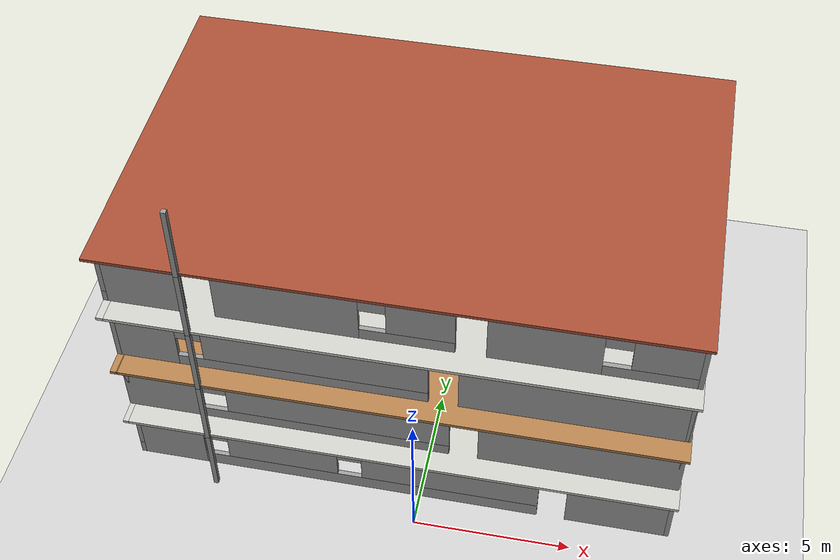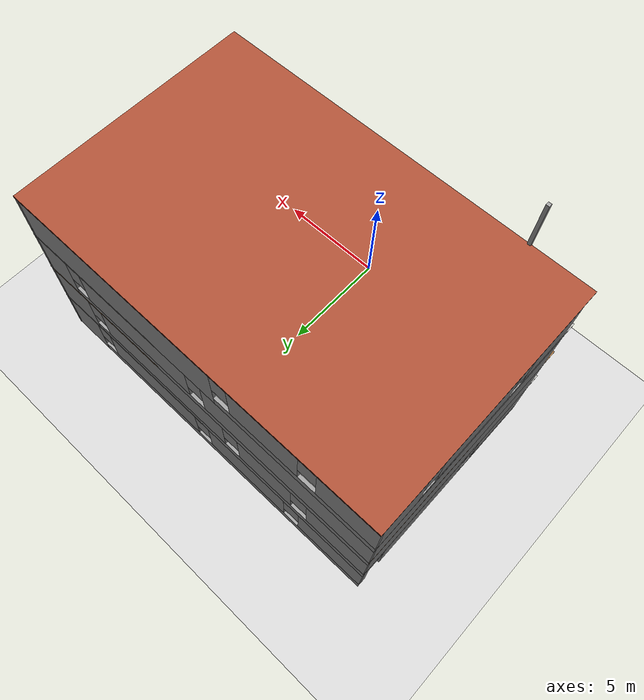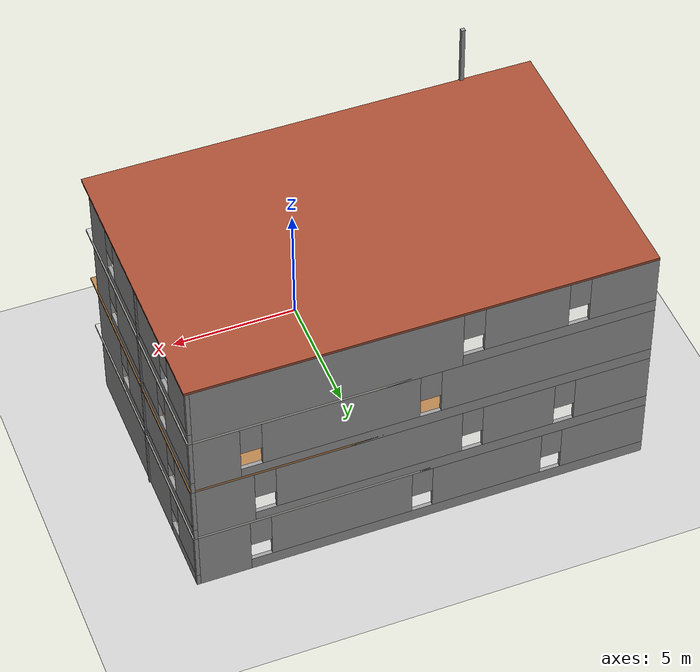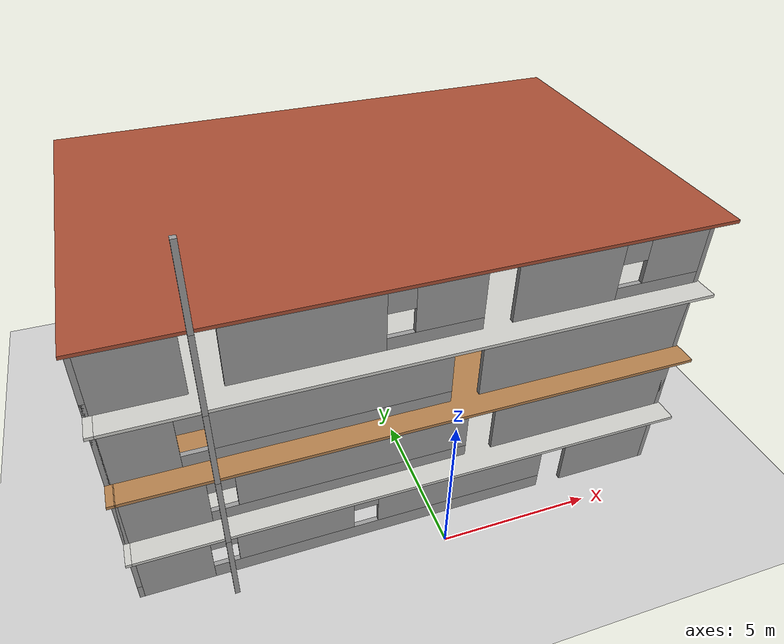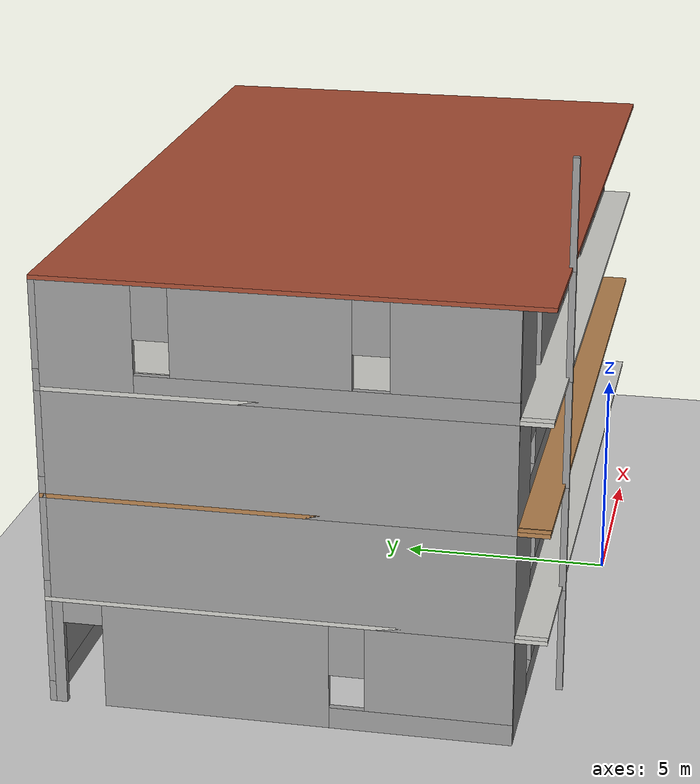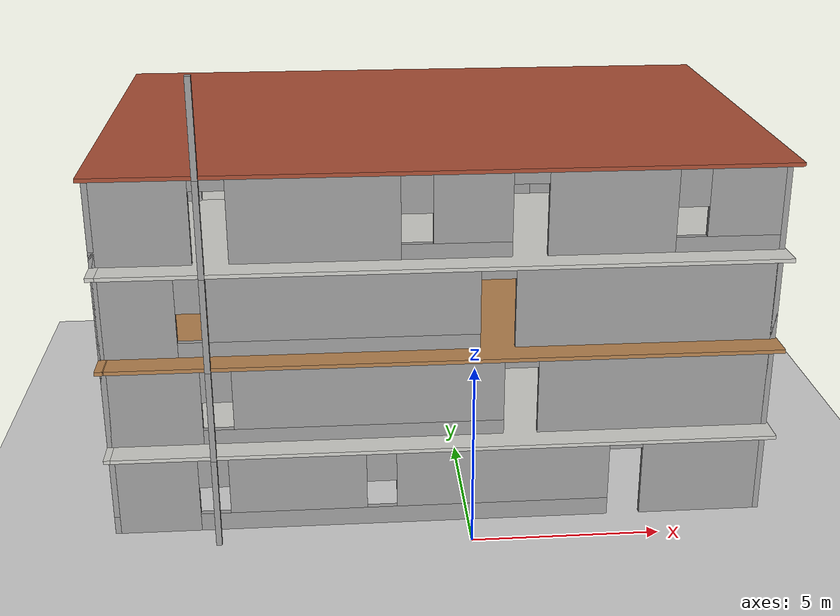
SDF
<sdf version="1.7">
 <world name="default">
  <light name="sun" type="directional">
   <pose>0 0 10 0 -0 0</pose>
   <diffuse>0.8 0.8 0.8 1</diffuse>
   <specular>0.2 0.2 0.2 1</specular>
   <attenuation>
    <range>1000</range>
    <constant>0.9</constant>
    <linear>0.01</linear>
    <quadratic>0.001</quadratic>
   </attenuation>
   <direction>-0.5 0.1 -0.9</direction>
   <spot><inner_angle>0</inner_angle><outer_angle>0</outer_angle><falloff>0</falloff></spot>
  </light>
  <model name="ground_plane">
   <static>1</static>
   <link name="link">
    <collision name="collision">
     <geometry><plane><normal>0 0 1</normal><size>100 100</size></plane></geometry>
     <surface>
      <contact><collide_bitmask>65535</collide_bitmask></contact>
      <friction><ode><mu>100</mu><mu2>50</mu2></ode></friction>
     </surface>
    </collision>
    <visual name="visual">
     <cast_shadows>0</cast_shadows>
     <geometry><plane><normal>0 0 1</normal><size>100 100</size></plane></geometry>
     <material>
      <script><uri>file://media/materials/scripts/gazebo.material</uri><name>Gazebo/Grey</name></script>
     </material>
    </visual>
   </link>
  </model>
  <plugin name="ros_interface_plugin" filename="librotors_gazebo_ros_interface_plugin.so"/>
  <physics name="default_physics" default="0" type="ode">
   <ode>
    <solver>
     <type>quick</type>
     <iters>10</iters>
     <sor>1.3</sor>
     <use_dynamic_moi_rescaling>0</use_dynamic_moi_rescaling>
    </solver>
    <constraints>
     <cfm>0</cfm>
     <erp>0.2</erp>
     <contact_max_correcting_vel>100</contact_max_correcting_vel>
     <contact_surface_layer>0.001</contact_surface_layer>
    </constraints>
   </ode>
   <max_step_size>0.002</max_step_size>
   <real_time_factor>1</real_time_factor>
   <real_time_update_rate>500</real_time_update_rate>
  </physics>
  <gravity>0 0 -9.8066</gravity>
  <magnetic_field>6e-06 2.3e-05 -4.2e-05</magnetic_field>
  <atmosphere type="adiabatic"/>
  <scene><ambient>0.4 0.4 0.4 1</ambient><background>0.7 0.7 0.7 1</background><shadows>1</shadows></scene>
  <spherical_coordinates>
   <surface_model>EARTH_WGS84</surface_model>
   <latitude_deg>0</latitude_deg>
   <longitude_deg>0</longitude_deg>
   <elevation>0</elevation>
   <heading_deg>0</heading_deg>
  </spherical_coordinates>
  <model name="saglam_yeni_bina1">
   <pose>-0.684997 5.87917 0 0 -0 0</pose>
   <link name="Floor_0">
    <pose>-5.97811 -5.5661 0 0 -0 0</pose>
    <visual name="Floor_0_Visual_0">
     <pose>0 0 0.05 0 -0 0</pose>
     <geometry><box><size>0 0 0.1</size></box></geometry>
     <material>
      <script><uri>file://media/materials/scripts/gazebo.material</uri><name>Gazebo/CeilingTiled</name></script>
      <ambient>0.435294 0.796078 0.67451 1</ambient>
     </material>
     <meta><layer>0</layer></meta>
    </visual>
    <collision name="Floor_0_Collision_0">
     <geometry><box><size>0 0 0.1</size></box></geometry>
     <pose>0 0 0.05 0 -0 0</pose>
    </collision>
   </link>
   <link name="Floor_4">
    <pose>0.000156 0.0375 2.5 0 -0 0</pose>
    <visual name="Floor_4_Visual_0">
     <pose>-8.68623 0 0.05 0 -0 0</pose>
     <geometry><box><size>0.173766 11.2072 0.1</size></box></geometry>
     <material>
      <script><uri>file://media/materials/scripts/gazebo.material</uri><name>Gazebo/CeilingTiled</name></script>
      <ambient>1 1 1 1</ambient>
     </material>
     <meta><layer>1</layer></meta>
    </visual>
    <collision name="Floor_4_Collision_0">
     <geometry><box><size>0.173766 11.2072 0.1</size></box></geometry>
     <pose>-8.68623 0 0.05 0 -0 0</pose>
    </collision>
    <visual name="Floor_4_Visual_1">
     <pose>0.086883 -2.61131 0.05 0 -0 0</pose>
     <geometry><box><size>17.3725 5.98458 0.1</size></box></geometry>
     <material>
      <script><uri>file://media/materials/scripts/gazebo.material</uri><name>Gazebo/CeilingTiled</name></script>
      <ambient>1 1 1 1</ambient>
     </material>
     <meta><layer>1</layer></meta>
    </visual>
    <collision name="Floor_4_Collision_1">
     <geometry><box><size>17.3725 5.98458 0.1</size></box></geometry>
     <pose>0.086883 -2.61131 0.05 0 -0 0</pose>
    </collision>
    <visual name="Floor_4_Visual_2">
     <pose>0.600108 2.99229 0.05 0 -0 0</pose>
     <geometry><box><size>16.346 5.22262 0.1</size></box></geometry>
     <material>
      <script><uri>file://media/materials/scripts/gazebo.material</uri><name>Gazebo/CeilingTiled</name></script>
      <ambient>1 1 1 1</ambient>
     </material>
     <meta><layer>1</layer></meta>
    </visual>
    <collision name="Floor_4_Collision_2">
     <geometry><box><size>16.346 5.22262 0.1</size></box></geometry>
     <pose>0.600108 2.99229 0.05 0 -0 0</pose>
    </collision>
    <visual name="Floor_4_Visual_3">
     <pose>-8.58612 4.74229 0.05 0 -0 0</pose>
     <geometry><box><size>0.02645 1.72262 0.1</size></box></geometry>
     <material>
      <script><uri>file://media/materials/scripts/gazebo.material</uri><name>Gazebo/CeilingTiled</name></script>
      <ambient>1 1 1 1</ambient>
     </material>
     <meta><layer>1</layer></meta>
    </visual>
    <collision name="Floor_4_Collision_3">
     <geometry><box><size>0.02645 1.72262 0.1</size></box></geometry>
     <pose>-8.58612 4.74229 0.05 0 -0 0</pose>
    </collision>
   </link>
   <link name="Floor_5">
    <pose>0.000156 0.0375 5 0 -0 0</pose>
    <visual name="Floor_5_Visual_0">
     <pose>-8.673 0 0.05 0 -0 0</pose>
     <geometry><box><size>0.200216 11.2072 0.1</size></box></geometry>
     <material>
      <script><uri>file://media/materials/scripts/gazebo.material</uri><name>Gazebo/Wood</name></script>
      <ambient>1 1 1 1</ambient>
     </material>
     <meta><layer>2</layer></meta>
    </visual>
    <collision name="Floor_5_Collision_0">
     <geometry><box><size>0.200216 11.2072 0.1</size></box></geometry>
     <pose>-8.673 0 0.05 0 -0 0</pose>
    </collision>
    <visual name="Floor_5_Visual_1">
     <pose>-8.55967 -2.61131 0.05 0 -0 0</pose>
     <geometry><box><size>0.02645 5.98458 0.1</size></box></geometry>
     <material>
      <script><uri>file://media/materials/scripts/gazebo.material</uri><name>Gazebo/Wood</name></script>
      <ambient>1 1 1 1</ambient>
     </material>
     <meta><layer>2</layer></meta>
    </visual>
    <collision name="Floor_5_Collision_1">
     <geometry><box><size>0.02645 5.98458 0.1</size></box></geometry>
     <pose>-8.55967 -2.61131 0.05 0 -0 0</pose>
    </collision>
    <visual name="Floor_5_Visual_2">
     <pose>0.113333 -2.62454 0.05 0 -0 0</pose>
     <geometry><box><size>17.3195 5.95813 0.1</size></box></geometry>
     <material>
      <script><uri>file://media/materials/scripts/gazebo.material</uri><name>Gazebo/Wood</name></script>
      <ambient>1 1 1 1</ambient>
     </material>
     <meta><layer>2</layer></meta>
    </visual>
    <collision name="Floor_5_Collision_2">
     <geometry><box><size>17.3195 5.95813 0.1</size></box></geometry>
     <pose>0.113333 -2.62454 0.05 0 -0 0</pose>
    </collision>
    <visual name="Floor_5_Visual_3">
     <pose>0.613333 2.97906 0.05 0 -0 0</pose>
     <geometry><box><size>16.3195 5.24907 0.1</size></box></geometry>
     <material>
      <script><uri>file://media/materials/scripts/gazebo.material</uri><name>Gazebo/Wood</name></script>
      <ambient>1 1 1 1</ambient>
     </material>
     <meta><layer>2</layer></meta>
    </visual>
    <collision name="Floor_5_Collision_3">
     <geometry><box><size>16.3195 5.24907 0.1</size></box></geometry>
     <pose>0.613333 2.97906 0.05 0 -0 0</pose>
    </collision>
    <visual name="Floor_5_Visual_4">
     <pose>-8.55967 4.74229 0.05 0 -0 0</pose>
     <geometry><box><size>0.02645 1.72262 0.1</size></box></geometry>
     <material>
      <script><uri>file://media/materials/scripts/gazebo.material</uri><name>Gazebo/Wood</name></script>
      <ambient>1 1 1 1</ambient>
     </material>
     <meta><layer>2</layer></meta>
    </visual>
    <collision name="Floor_5_Collision_4">
     <geometry><box><size>0.02645 1.72262 0.1</size></box></geometry>
     <pose>-8.55967 4.74229 0.05 0 -0 0</pose>
    </collision>
   </link>
   <link name="Floor_6">
    <pose>0.000156 0.0375 7.5 0 -0 0</pose>
    <visual name="Floor_6_Visual_0">
     <pose>-8.65977 0 0.05 0 -0 0</pose>
     <geometry><box><size>0.226666 11.2072 0.1</size></box></geometry>
     <material>
      <script><uri>file://media/materials/scripts/gazebo.material</uri><name>Gazebo/CeilingTiled</name></script>
      <ambient>1 1 1 1</ambient>
     </material>
     <meta><layer>3</layer></meta>
    </visual>
    <collision name="Floor_6_Collision_0">
     <geometry><box><size>0.226666 11.2072 0.1</size></box></geometry>
     <pose>-8.65977 0 0.05 0 -0 0</pose>
    </collision>
    <visual name="Floor_6_Visual_1">
     <pose>0.113333 -2.62454 0.05 0 -0 0</pose>
     <geometry><box><size>17.3195 5.95813 0.1</size></box></geometry>
     <material>
      <script><uri>file://media/materials/scripts/gazebo.material</uri><name>Gazebo/CeilingTiled</name></script>
      <ambient>1 1 1 1</ambient>
     </material>
     <meta><layer>3</layer></meta>
    </visual>
    <collision name="Floor_6_Collision_1">
     <geometry><box><size>17.3195 5.95813 0.1</size></box></geometry>
     <pose>0.113333 -2.62454 0.05 0 -0 0</pose>
    </collision>
    <visual name="Floor_6_Visual_2">
     <pose>0.613333 2.97906 0.05 0 -0 0</pose>
     <geometry><box><size>16.3195 5.24907 0.1</size></box></geometry>
     <material>
      <script><uri>file://media/materials/scripts/gazebo.material</uri><name>Gazebo/CeilingTiled</name></script>
      <ambient>1 1 1 1</ambient>
     </material>
     <meta><layer>3</layer></meta>
    </visual>
    <collision name="Floor_6_Collision_2">
     <geometry><box><size>16.3195 5.24907 0.1</size></box></geometry>
     <pose>0.613333 2.97906 0.05 0 -0 0</pose>
    </collision>
    <visual name="Floor_6_Visual_3">
     <pose>-8.04644 4.72906 0.05 0 -0 0</pose>
     <geometry><box><size>1 1.74907 0.1</size></box></geometry>
     <material>
      <script><uri>file://media/materials/scripts/gazebo.material</uri><name>Gazebo/CeilingTiled</name></script>
      <ambient>1 1 1 1</ambient>
     </material>
     <meta><layer>3</layer></meta>
    </visual>
    <collision name="Floor_6_Collision_3">
     <geometry><box><size>1 1.74907 0.1</size></box></geometry>
     <pose>-8.04644 4.72906 0.05 0 -0 0</pose>
    </collision>
   </link>
   <link name="Floor_8">
    <collision name="Floor_8_Collision">
     <geometry><box><size>17.5462 11.2072 0.1</size></box></geometry>
     <pose>0 0 0.05 0 -0 0</pose>
    </collision>
    <visual name="Floor_8_Visual">
     <pose>0 0 0.05 0 -0 0</pose>
     <geometry><box><size>17.5462 11.2072 0.1</size></box></geometry>
     <material>
      <script><uri>file://media/materials/scripts/gazebo.material</uri><name>Gazebo/Bricks</name></script>
      <ambient>0.921569 0.807843 0.615686 1</ambient>
     </material>
     <meta><layer>4</layer></meta>
    </visual>
    <pose>-0.000157 0.037447 10 0 -0 0</pose>
   </link>
   <link name="Stairs_1">
    <visual name="Stairs_1_Visual_0">
     <pose>-8.09919 3.80181 0.083333 0 -0 0</pose>
     <geometry><box><size>1 0.233333 0.166667</size></box></geometry>
     <material>
      <script><uri>file://media/materials/scripts/gazebo.material</uri><name>Gazebo/Grey</name></script>
      <ambient>1 1 1 1</ambient>
     </material>
     <meta><layer>0</layer></meta>
    </visual>
    <collision name="Stairs_1_Collision_0">
     <geometry><box><size>1 0.233333 0.166667</size></box></geometry>
     <pose>-8.09919 3.80181 0.083333 0 -0 0</pose>
    </collision>
    <visual name="Stairs_1_Visual_1">
     <pose>-8.09919 3.56848 0.25 0 -0 0</pose>
     <geometry><box><size>1 0.233333 0.166667</size></box></geometry>
     <material>
      <script><uri>file://media/materials/scripts/gazebo.material</uri><name>Gazebo/Grey</name></script>
      <ambient>1 1 1 1</ambient>
     </material>
     <meta><layer>0</layer></meta>
    </visual>
    <collision name="Stairs_1_Collision_1">
     <geometry><box><size>1 0.233333 0.166667</size></box></geometry>
     <pose>-8.09919 3.56848 0.25 0 -0 0</pose>
    </collision>
    <visual name="Stairs_1_Visual_2">
     <pose>-8.09919 3.33514 0.416667 0 -0 0</pose>
     <geometry><box><size>1 0.233333 0.166667</size></box></geometry>
     <material>
      <script><uri>file://media/materials/scripts/gazebo.material</uri><name>Gazebo/Grey</name></script>
      <ambient>1 1 1 1</ambient>
     </material>
     <meta><layer>0</layer></meta>
    </visual>
    <collision name="Stairs_1_Collision_2">
     <geometry><box><size>1 0.233333 0.166667</size></box></geometry>
     <pose>-8.09919 3.33514 0.416667 0 -0 0</pose>
    </collision>
    <visual name="Stairs_1_Visual_3">
     <pose>-8.09919 3.10181 0.583333 0 -0 0</pose>
     <geometry><box><size>1 0.233333 0.166667</size></box></geometry>
     <material>
      <script><uri>file://media/materials/scripts/gazebo.material</uri><name>Gazebo/Grey</name></script>
      <ambient>1 1 1 1</ambient>
     </material>
     <meta><layer>0</layer></meta>
    </visual>
    <collision name="Stairs_1_Collision_3">
     <geometry><box><size>1 0.233333 0.166667</size></box></geometry>
     <pose>-8.09919 3.10181 0.583333 0 -0 0</pose>
    </collision>
    <visual name="Stairs_1_Visual_4">
     <pose>-8.09919 2.86848 0.75 0 -0 0</pose>
     <geometry><box><size>1 0.233333 0.166667</size></box></geometry>
     <material>
      <script><uri>file://media/materials/scripts/gazebo.material</uri><name>Gazebo/Grey</name></script>
      <ambient>1 1 1 1</ambient>
     </material>
     <meta><layer>0</layer></meta>
    </visual>
    <collision name="Stairs_1_Collision_4">
     <geometry><box><size>1 0.233333 0.166667</size></box></geometry>
     <pose>-8.09919 2.86848 0.75 0 -0 0</pose>
    </collision>
    <visual name="Stairs_1_Visual_5">
     <pose>-8.09919 2.63514 0.916667 0 -0 0</pose>
     <geometry><box><size>1 0.233333 0.166667</size></box></geometry>
     <material>
      <script><uri>file://media/materials/scripts/gazebo.material</uri><name>Gazebo/Grey</name></script>
      <ambient>1 1 1 1</ambient>
     </material>
     <meta><layer>0</layer></meta>
    </visual>
    <collision name="Stairs_1_Collision_5">
     <geometry><box><size>1 0.233333 0.166667</size></box></geometry>
     <pose>-8.09919 2.63514 0.916667 0 -0 0</pose>
    </collision>
    <visual name="Stairs_1_Visual_6">
     <pose>-8.09919 2.40181 1.08333 0 -0 0</pose>
     <geometry><box><size>1 0.233333 0.166667</size></box></geometry>
     <material>
      <script><uri>file://media/materials/scripts/gazebo.material</uri><name>Gazebo/Grey</name></script>
      <ambient>1 1 1 1</ambient>
     </material>
     <meta><layer>0</layer></meta>
    </visual>
    <collision name="Stairs_1_Collision_6">
     <geometry><box><size>1 0.233333 0.166667</size></box></geometry>
     <pose>-8.09919 2.40181 1.08333 0 -0 0</pose>
    </collision>
    <visual name="Stairs_1_Visual_7">
     <pose>-8.09919 2.16848 1.25 0 -0 0</pose>
     <geometry><box><size>1 0.233333 0.166667</size></box></geometry>
     <material>
      <script><uri>file://media/materials/scripts/gazebo.material</uri><name>Gazebo/Grey</name></script>
      <ambient>1 1 1 1</ambient>
     </material>
     <meta><layer>0</layer></meta>
    </visual>
    <collision name="Stairs_1_Collision_7">
     <geometry><box><size>1 0.233333 0.166667</size></box></geometry>
     <pose>-8.09919 2.16848 1.25 0 -0 0</pose>
    </collision>
    <visual name="Stairs_1_Visual_8">
     <pose>-8.09919 1.93514 1.41667 0 -0 0</pose>
     <geometry><box><size>1 0.233333 0.166667</size></box></geometry>
     <material>
      <script><uri>file://media/materials/scripts/gazebo.material</uri><name>Gazebo/Grey</name></script>
      <ambient>1 1 1 1</ambient>
     </material>
     <meta><layer>0</layer></meta>
    </visual>
    <collision name="Stairs_1_Collision_8">
     <geometry><box><size>1 0.233333 0.166667</size></box></geometry>
     <pose>-8.09919 1.93514 1.41667 0 -0 0</pose>
    </collision>
    <visual name="Stairs_1_Visual_9">
     <pose>-8.09919 1.70181 1.58333 0 -0 0</pose>
     <geometry><box><size>1 0.233333 0.166667</size></box></geometry>
     <material>
      <script><uri>file://media/materials/scripts/gazebo.material</uri><name>Gazebo/Grey</name></script>
      <ambient>1 1 1 1</ambient>
     </material>
     <meta><layer>0</layer></meta>
    </visual>
    <collision name="Stairs_1_Collision_9">
     <geometry><box><size>1 0.233333 0.166667</size></box></geometry>
     <pose>-8.09919 1.70181 1.58333 0 -0 0</pose>
    </collision>
    <visual name="Stairs_1_Visual_10">
     <pose>-8.09919 1.46848 1.75 0 -0 0</pose>
     <geometry><box><size>1 0.233333 0.166667</size></box></geometry>
     <material>
      <script><uri>file://media/materials/scripts/gazebo.material</uri><name>Gazebo/Grey</name></script>
      <ambient>1 1 1 1</ambient>
     </material>
     <meta><layer>0</layer></meta>
    </visual>
    <collision name="Stairs_1_Collision_10">
     <geometry><box><size>1 0.233333 0.166667</size></box></geometry>
     <pose>-8.09919 1.46848 1.75 0 -0 0</pose>
    </collision>
    <visual name="Stairs_1_Visual_11">
     <pose>-8.09919 1.23514 1.91667 0 -0 0</pose>
     <geometry><box><size>1 0.233333 0.166667</size></box></geometry>
     <material>
      <script><uri>file://media/materials/scripts/gazebo.material</uri><name>Gazebo/Grey</name></script>
      <ambient>1 1 1 1</ambient>
     </material>
     <meta><layer>0</layer></meta>
    </visual>
    <collision name="Stairs_1_Collision_11">
     <geometry><box><size>1 0.233333 0.166667</size></box></geometry>
     <pose>-8.09919 1.23514 1.91667 0 -0 0</pose>
    </collision>
    <visual name="Stairs_1_Visual_12">
     <pose>-8.09919 1.00181 2.08333 0 -0 0</pose>
     <geometry><box><size>1 0.233333 0.166667</size></box></geometry>
     <material>
      <script><uri>file://media/materials/scripts/gazebo.material</uri><name>Gazebo/Grey</name></script>
      <ambient>1 1 1 1</ambient>
     </material>
     <meta><layer>0</layer></meta>
    </visual>
    <collision name="Stairs_1_Collision_12">
     <geometry><box><size>1 0.233333 0.166667</size></box></geometry>
     <pose>-8.09919 1.00181 2.08333 0 -0 0</pose>
    </collision>
    <visual name="Stairs_1_Visual_13">
     <pose>-8.09919 0.768477 2.25 0 -0 0</pose>
     <geometry><box><size>1 0.233333 0.166667</size></box></geometry>
     <material>
      <script><uri>file://media/materials/scripts/gazebo.material</uri><name>Gazebo/Grey</name></script>
      <ambient>1 1 1 1</ambient>
     </material>
     <meta><layer>0</layer></meta>
    </visual>
    <collision name="Stairs_1_Collision_13">
     <geometry><box><size>1 0.233333 0.166667</size></box></geometry>
     <pose>-8.09919 0.768477 2.25 0 -0 0</pose>
    </collision>
    <visual name="Stairs_1_Visual_14">
     <pose>-8.09919 0.535143 2.41667 0 -0 0</pose>
     <geometry><box><size>1 0.233333 0.166667</size></box></geometry>
     <material>
      <script><uri>file://media/materials/scripts/gazebo.material</uri><name>Gazebo/Grey</name></script>
      <ambient>1 1 1 1</ambient>
     </material>
     <meta><layer>0</layer></meta>
    </visual>
    <collision name="Stairs_1_Collision_14">
     <geometry><box><size>1 0.233333 0.166667</size></box></geometry>
     <pose>-8.09919 0.535143 2.41667 0 -0 0</pose>
    </collision>
   </link>
   <link name="Stairs_2">
    <visual name="Stairs_2_Visual_0">
     <pose>-8.07274 3.80181 2.58333 0 -0 0</pose>
     <geometry><box><size>1 0.233333 0.166667</size></box></geometry>
     <material>
      <script><uri>file://media/materials/scripts/gazebo.material</uri><name>Gazebo/Grey</name></script>
      <ambient>1 1 1 1</ambient>
     </material>
     <meta><layer>1</layer></meta>
    </visual>
    <collision name="Stairs_2_Collision_0">
     <geometry><box><size>1 0.233333 0.166667</size></box></geometry>
     <pose>-8.07274 3.80181 2.58333 0 -0 0</pose>
    </collision>
    <visual name="Stairs_2_Visual_1">
     <pose>-8.07274 3.56848 2.75 0 -0 0</pose>
     <geometry><box><size>1 0.233333 0.166667</size></box></geometry>
     <material>
      <script><uri>file://media/materials/scripts/gazebo.material</uri><name>Gazebo/Grey</name></script>
      <ambient>1 1 1 1</ambient>
     </material>
     <meta><layer>1</layer></meta>
    </visual>
    <collision name="Stairs_2_Collision_1">
     <geometry><box><size>1 0.233333 0.166667</size></box></geometry>
     <pose>-8.07274 3.56848 2.75 0 -0 0</pose>
    </collision>
    <visual name="Stairs_2_Visual_2">
     <pose>-8.07274 3.33514 2.91667 0 -0 0</pose>
     <geometry><box><size>1 0.233333 0.166667</size></box></geometry>
     <material>
      <script><uri>file://media/materials/scripts/gazebo.material</uri><name>Gazebo/Grey</name></script>
      <ambient>1 1 1 1</ambient>
     </material>
     <meta><layer>1</layer></meta>
    </visual>
    <collision name="Stairs_2_Collision_2">
     <geometry><box><size>1 0.233333 0.166667</size></box></geometry>
     <pose>-8.07274 3.33514 2.91667 0 -0 0</pose>
    </collision>
    <visual name="Stairs_2_Visual_3">
     <pose>-8.07274 3.10181 3.08333 0 -0 0</pose>
     <geometry><box><size>1 0.233333 0.166667</size></box></geometry>
     <material>
      <script><uri>file://media/materials/scripts/gazebo.material</uri><name>Gazebo/Grey</name></script>
      <ambient>1 1 1 1</ambient>
     </material>
     <meta><layer>1</layer></meta>
    </visual>
    <collision name="Stairs_2_Collision_3">
     <geometry><box><size>1 0.233333 0.166667</size></box></geometry>
     <pose>-8.07274 3.10181 3.08333 0 -0 0</pose>
    </collision>
    <visual name="Stairs_2_Visual_4">
     <pose>-8.07274 2.86848 3.25 0 -0 0</pose>
     <geometry><box><size>1 0.233333 0.166667</size></box></geometry>
     <material>
      <script><uri>file://media/materials/scripts/gazebo.material</uri><name>Gazebo/Grey</name></script>
      <ambient>1 1 1 1</ambient>
     </material>
     <meta><layer>1</layer></meta>
    </visual>
    <collision name="Stairs_2_Collision_4">
     <geometry><box><size>1 0.233333 0.166667</size></box></geometry>
     <pose>-8.07274 2.86848 3.25 0 -0 0</pose>
    </collision>
    <visual name="Stairs_2_Visual_5">
     <pose>-8.07274 2.63514 3.41667 0 -0 0</pose>
     <geometry><box><size>1 0.233333 0.166667</size></box></geometry>
     <material>
      <script><uri>file://media/materials/scripts/gazebo.material</uri><name>Gazebo/Grey</name></script>
      <ambient>1 1 1 1</ambient>
     </material>
     <meta><layer>1</layer></meta>
    </visual>
    <collision name="Stairs_2_Collision_5">
     <geometry><box><size>1 0.233333 0.166667</size></box></geometry>
     <pose>-8.07274 2.63514 3.41667 0 -0 0</pose>
    </collision>
    <visual name="Stairs_2_Visual_6">
     <pose>-8.07274 2.40181 3.58333 0 -0 0</pose>
     <geometry><box><size>1 0.233333 0.166667</size></box></geometry>
     <material>
      <script><uri>file://media/materials/scripts/gazebo.material</uri><name>Gazebo/Grey</name></script>
      <ambient>1 1 1 1</ambient>
     </material>
     <meta><layer>1</layer></meta>
    </visual>
    <collision name="Stairs_2_Collision_6">
     <geometry><box><size>1 0.233333 0.166667</size></box></geometry>
     <pose>-8.07274 2.40181 3.58333 0 -0 0</pose>
    </collision>
    <visual name="Stairs_2_Visual_7">
     <pose>-8.07274 2.16848 3.75 0 -0 0</pose>
     <geometry><box><size>1 0.233333 0.166667</size></box></geometry>
     <material>
      <script><uri>file://media/materials/scripts/gazebo.material</uri><name>Gazebo/Grey</name></script>
      <ambient>1 1 1 1</ambient>
     </material>
     <meta><layer>1</layer></meta>
    </visual>
    <collision name="Stairs_2_Collision_7">
     <geometry><box><size>1 0.233333 0.166667</size></box></geometry>
     <pose>-8.07274 2.16848 3.75 0 -0 0</pose>
    </collision>
    <visual name="Stairs_2_Visual_8">
     <pose>-8.07274 1.93514 3.91667 0 -0 0</pose>
     <geometry><box><size>1 0.233333 0.166667</size></box></geometry>
     <material>
      <script><uri>file://media/materials/scripts/gazebo.material</uri><name>Gazebo/Grey</name></script>
      <ambient>1 1 1 1</ambient>
     </material>
     <meta><layer>1</layer></meta>
    </visual>
    <collision name="Stairs_2_Collision_8">
     <geometry><box><size>1 0.233333 0.166667</size></box></geometry>
     <pose>-8.07274 1.93514 3.91667 0 -0 0</pose>
    </collision>
    <visual name="Stairs_2_Visual_9">
     <pose>-8.07274 1.70181 4.08333 0 -0 0</pose>
     <geometry><box><size>1 0.233333 0.166667</size></box></geometry>
     <material>
      <script><uri>file://media/materials/scripts/gazebo.material</uri><name>Gazebo/Grey</name></script>
      <ambient>1 1 1 1</ambient>
     </material>
     <meta><layer>1</layer></meta>
    </visual>
    <collision name="Stairs_2_Collision_9">
     <geometry><box><size>1 0.233333 0.166667</size></box></geometry>
     <pose>-8.07274 1.70181 4.08333 0 -0 0</pose>
    </collision>
    <visual name="Stairs_2_Visual_10">
     <pose>-8.07274 1.46848 4.25 0 -0 0</pose>
     <geometry><box><size>1 0.233333 0.166667</size></box></geometry>
     <material>
      <script><uri>file://media/materials/scripts/gazebo.material</uri><name>Gazebo/Grey</name></script>
      <ambient>1 1 1 1</ambient>
     </material>
     <meta><layer>1</layer></meta>
    </visual>
    <collision name="Stairs_2_Collision_10">
     <geometry><box><size>1 0.233333 0.166667</size></box></geometry>
     <pose>-8.07274 1.46848 4.25 0 -0 0</pose>
    </collision>
    <visual name="Stairs_2_Visual_11">
     <pose>-8.07274 1.23514 4.41667 0 -0 0</pose>
     <geometry><box><size>1 0.233333 0.166667</size></box></geometry>
     <material>
      <script><uri>file://media/materials/scripts/gazebo.material</uri><name>Gazebo/Grey</name></script>
      <ambient>1 1 1 1</ambient>
     </material>
     <meta><layer>1</layer></meta>
    </visual>
    <collision name="Stairs_2_Collision_11">
     <geometry><box><size>1 0.233333 0.166667</size></box></geometry>
     <pose>-8.07274 1.23514 4.41667 0 -0 0</pose>
    </collision>
    <visual name="Stairs_2_Visual_12">
     <pose>-8.07274 1.00181 4.58333 0 -0 0</pose>
     <geometry><box><size>1 0.233333 0.166667</size></box></geometry>
     <material>
      <script><uri>file://media/materials/scripts/gazebo.material</uri><name>Gazebo/Grey</name></script>
      <ambient>1 1 1 1</ambient>
     </material>
     <meta><layer>1</layer></meta>
    </visual>
    <collision name="Stairs_2_Collision_12">
     <geometry><box><size>1 0.233333 0.166667</size></box></geometry>
     <pose>-8.07274 1.00181 4.58333 0 -0 0</pose>
    </collision>
    <visual name="Stairs_2_Visual_13">
     <pose>-8.07274 0.768477 4.75 0 -0 0</pose>
     <geometry><box><size>1 0.233333 0.166667</size></box></geometry>
     <material>
      <script><uri>file://media/materials/scripts/gazebo.material</uri><name>Gazebo/Grey</name></script>
      <ambient>1 1 1 1</ambient>
     </material>
     <meta><layer>1</layer></meta>
    </visual>
    <collision name="Stairs_2_Collision_13">
     <geometry><box><size>1 0.233333 0.166667</size></box></geometry>
     <pose>-8.07274 0.768477 4.75 0 -0 0</pose>
    </collision>
    <visual name="Stairs_2_Visual_14">
     <pose>-8.07274 0.535143 4.91667 0 -0 0</pose>
     <geometry><box><size>1 0.233333 0.166667</size></box></geometry>
     <material>
      <script><uri>file://media/materials/scripts/gazebo.material</uri><name>Gazebo/Grey</name></script>
      <ambient>1 1 1 1</ambient>
     </material>
     <meta><layer>1</layer></meta>
    </visual>
    <collision name="Stairs_2_Collision_14">
     <geometry><box><size>1 0.233333 0.166667</size></box></geometry>
     <pose>-8.07274 0.535143 4.91667 0 -0 0</pose>
    </collision>
   </link>
   <link name="Stairs_3">
    <visual name="Stairs_3_Visual_0">
     <pose>-8.04629 3.77536 5.08333 0 -0 0</pose>
     <geometry><box><size>1 0.233333 0.166667</size></box></geometry>
     <material>
      <script><uri>file://media/materials/scripts/gazebo.material</uri><name>Gazebo/Grey</name></script>
      <ambient>1 1 1 1</ambient>
     </material>
     <meta><layer>2</layer></meta>
    </visual>
    <collision name="Stairs_3_Collision_0">
     <geometry><box><size>1 0.233333 0.166667</size></box></geometry>
     <pose>-8.04629 3.77536 5.08333 0 -0 0</pose>
    </collision>
    <visual name="Stairs_3_Visual_1">
     <pose>-8.04629 3.54203 5.25 0 -0 0</pose>
     <geometry><box><size>1 0.233333 0.166667</size></box></geometry>
     <material>
      <script><uri>file://media/materials/scripts/gazebo.material</uri><name>Gazebo/Grey</name></script>
      <ambient>1 1 1 1</ambient>
     </material>
     <meta><layer>2</layer></meta>
    </visual>
    <collision name="Stairs_3_Collision_1">
     <geometry><box><size>1 0.233333 0.166667</size></box></geometry>
     <pose>-8.04629 3.54203 5.25 0 -0 0</pose>
    </collision>
    <visual name="Stairs_3_Visual_2">
     <pose>-8.04629 3.30869 5.41667 0 -0 0</pose>
     <geometry><box><size>1 0.233333 0.166667</size></box></geometry>
     <material>
      <script><uri>file://media/materials/scripts/gazebo.material</uri><name>Gazebo/Grey</name></script>
      <ambient>1 1 1 1</ambient>
     </material>
     <meta><layer>2</layer></meta>
    </visual>
    <collision name="Stairs_3_Collision_2">
     <geometry><box><size>1 0.233333 0.166667</size></box></geometry>
     <pose>-8.04629 3.30869 5.41667 0 -0 0</pose>
    </collision>
    <visual name="Stairs_3_Visual_3">
     <pose>-8.04629 3.07536 5.58333 0 -0 0</pose>
     <geometry><box><size>1 0.233333 0.166667</size></box></geometry>
     <material>
      <script><uri>file://media/materials/scripts/gazebo.material</uri><name>Gazebo/Grey</name></script>
      <ambient>1 1 1 1</ambient>
     </material>
     <meta><layer>2</layer></meta>
    </visual>
    <collision name="Stairs_3_Collision_3">
     <geometry><box><size>1 0.233333 0.166667</size></box></geometry>
     <pose>-8.04629 3.07536 5.58333 0 -0 0</pose>
    </collision>
    <visual name="Stairs_3_Visual_4">
     <pose>-8.04629 2.84203 5.75 0 -0 0</pose>
     <geometry><box><size>1 0.233333 0.166667</size></box></geometry>
     <material>
      <script><uri>file://media/materials/scripts/gazebo.material</uri><name>Gazebo/Grey</name></script>
      <ambient>1 1 1 1</ambient>
     </material>
     <meta><layer>2</layer></meta>
    </visual>
    <collision name="Stairs_3_Collision_4">
     <geometry><box><size>1 0.233333 0.166667</size></box></geometry>
     <pose>-8.04629 2.84203 5.75 0 -0 0</pose>
    </collision>
    <visual name="Stairs_3_Visual_5">
     <pose>-8.04629 2.60869 5.91667 0 -0 0</pose>
     <geometry><box><size>1 0.233333 0.166667</size></box></geometry>
     <material>
      <script><uri>file://media/materials/scripts/gazebo.material</uri><name>Gazebo/Grey</name></script>
      <ambient>1 1 1 1</ambient>
     </material>
     <meta><layer>2</layer></meta>
    </visual>
    <collision name="Stairs_3_Collision_5">
     <geometry><box><size>1 0.233333 0.166667</size></box></geometry>
     <pose>-8.04629 2.60869 5.91667 0 -0 0</pose>
    </collision>
    <visual name="Stairs_3_Visual_6">
     <pose>-8.04629 2.37536 6.08333 0 -0 0</pose>
     <geometry><box><size>1 0.233333 0.166667</size></box></geometry>
     <material>
      <script><uri>file://media/materials/scripts/gazebo.material</uri><name>Gazebo/Grey</name></script>
      <ambient>1 1 1 1</ambient>
     </material>
     <meta><layer>2</layer></meta>
    </visual>
    <collision name="Stairs_3_Collision_6">
     <geometry><box><size>1 0.233333 0.166667</size></box></geometry>
     <pose>-8.04629 2.37536 6.08333 0 -0 0</pose>
    </collision>
    <visual name="Stairs_3_Visual_7">
     <pose>-8.04629 2.14203 6.25 0 -0 0</pose>
     <geometry><box><size>1 0.233333 0.166667</size></box></geometry>
     <material>
      <script><uri>file://media/materials/scripts/gazebo.material</uri><name>Gazebo/Grey</name></script>
      <ambient>1 1 1 1</ambient>
     </material>
     <meta><layer>2</layer></meta>
    </visual>
    <collision name="Stairs_3_Collision_7">
     <geometry><box><size>1 0.233333 0.166667</size></box></geometry>
     <pose>-8.04629 2.14203 6.25 0 -0 0</pose>
    </collision>
    <visual name="Stairs_3_Visual_8">
     <pose>-8.04629 1.90869 6.41667 0 -0 0</pose>
     <geometry><box><size>1 0.233333 0.166667</size></box></geometry>
     <material>
      <script><uri>file://media/materials/scripts/gazebo.material</uri><name>Gazebo/Grey</name></script>
      <ambient>1 1 1 1</ambient>
     </material>
     <meta><layer>2</layer></meta>
    </visual>
    <collision name="Stairs_3_Collision_8">
     <geometry><box><size>1 0.233333 0.166667</size></box></geometry>
     <pose>-8.04629 1.90869 6.41667 0 -0 0</pose>
    </collision>
    <visual name="Stairs_3_Visual_9">
     <pose>-8.04629 1.67536 6.58333 0 -0 0</pose>
     <geometry><box><size>1 0.233333 0.166667</size></box></geometry>
     <material>
      <script><uri>file://media/materials/scripts/gazebo.material</uri><name>Gazebo/Grey</name></script>
      <ambient>1 1 1 1</ambient>
     </material>
     <meta><layer>2</layer></meta>
    </visual>
    <collision name="Stairs_3_Collision_9">
     <geometry><box><size>1 0.233333 0.166667</size></box></geometry>
     <pose>-8.04629 1.67536 6.58333 0 -0 0</pose>
    </collision>
    <visual name="Stairs_3_Visual_10">
     <pose>-8.04629 1.44203 6.75 0 -0 0</pose>
     <geometry><box><size>1 0.233333 0.166667</size></box></geometry>
     <material>
      <script><uri>file://media/materials/scripts/gazebo.material</uri><name>Gazebo/Grey</name></script>
      <ambient>1 1 1 1</ambient>
     </material>
     <meta><layer>2</layer></meta>
    </visual>
    <collision name="Stairs_3_Collision_10">
     <geometry><box><size>1 0.233333 0.166667</size></box></geometry>
     <pose>-8.04629 1.44203 6.75 0 -0 0</pose>
    </collision>
    <visual name="Stairs_3_Visual_11">
     <pose>-8.04629 1.20869 6.91667 0 -0 0</pose>
     <geometry><box><size>1 0.233333 0.166667</size></box></geometry>
     <material>
      <script><uri>file://media/materials/scripts/gazebo.material</uri><name>Gazebo/Grey</name></script>
      <ambient>1 1 1 1</ambient>
     </material>
     <meta><layer>2</layer></meta>
    </visual>
    <collision name="Stairs_3_Collision_11">
     <geometry><box><size>1 0.233333 0.166667</size></box></geometry>
     <pose>-8.04629 1.20869 6.91667 0 -0 0</pose>
    </collision>
    <visual name="Stairs_3_Visual_12">
     <pose>-8.04629 0.97536 7.08333 0 -0 0</pose>
     <geometry><box><size>1 0.233333 0.166667</size></box></geometry>
     <material>
      <script><uri>file://media/materials/scripts/gazebo.material</uri><name>Gazebo/Grey</name></script>
      <ambient>1 1 1 1</ambient>
     </material>
     <meta><layer>2</layer></meta>
    </visual>
    <collision name="Stairs_3_Collision_12">
     <geometry><box><size>1 0.233333 0.166667</size></box></geometry>
     <pose>-8.04629 0.97536 7.08333 0 -0 0</pose>
    </collision>
    <visual name="Stairs_3_Visual_13">
     <pose>-8.04629 0.742026 7.25 0 -0 0</pose>
     <geometry><box><size>1 0.233333 0.166667</size></box></geometry>
     <material>
      <script><uri>file://media/materials/scripts/gazebo.material</uri><name>Gazebo/Grey</name></script>
      <ambient>1 1 1 1</ambient>
     </material>
     <meta><layer>2</layer></meta>
    </visual>
    <collision name="Stairs_3_Collision_13">
     <geometry><box><size>1 0.233333 0.166667</size></box></geometry>
     <pose>-8.04629 0.742026 7.25 0 -0 0</pose>
    </collision>
    <visual name="Stairs_3_Visual_14">
     <pose>-8.04629 0.508693 7.41667 0 -0 0</pose>
     <geometry><box><size>1 0.233333 0.166667</size></box></geometry>
     <material>
      <script><uri>file://media/materials/scripts/gazebo.material</uri><name>Gazebo/Grey</name></script>
      <ambient>1 1 1 1</ambient>
     </material>
     <meta><layer>2</layer></meta>
    </visual>
    <collision name="Stairs_3_Collision_14">
     <geometry><box><size>1 0.233333 0.166667</size></box></geometry>
     <pose>-8.04629 0.508693 7.41667 0 -0 0</pose>
    </collision>
   </link>
   <link name="Wall_3">
    <collision name="Wall_3_Collision">
     <geometry><box><size>0.15 0.15 2.5</size></box></geometry>
     <pose>0 0 1.25 0 -0 0</pose>
    </collision>
    <visual name="Wall_3_Visual">
     <pose>0 0 1.25 0 -0 0</pose>
     <geometry><box><size>0.15 0.15 2.5</size></box></geometry>
     <material>
      <script><uri>file://media/materials/scripts/gazebo.material</uri><name>Gazebo/Grey</name></script>
      <ambient>1 1 1 1</ambient>
     </material>
     <meta><layer>0</layer></meta>
    </visual>
    <pose>-5.97811 -5.5661 0 0 -0 0</pose>
   </link>
   <link name="Wall_32">
    <pose>-0.022952 -4.7839 0 0 -0 0</pose>
    <visual name="Wall_32_Visual_0">
     <pose>-7.60802 0 1.25 0 -0 0</pose>
     <geometry><box><size>2.28397 0.15 2.5</size></box></geometry>
     <material>
      <script><uri>file://media/materials/scripts/gazebo.material</uri><name>Gazebo/Grey</name></script>
      <ambient>1 1 1 1</ambient>
     </material>
     <meta><layer>0</layer></meta>
    </visual>
    <collision name="Wall_32_Collision_0">
     <geometry><box><size>2.28397 0.15 2.5</size></box></geometry>
     <pose>-7.60802 0 1.25 0 -0 0</pose>
    </collision>
    <visual name="Wall_32_Visual_1">
     <pose>7.08181 0 1.25 0 -0 0</pose>
     <geometry><box><size>3.33638 0.15 2.5</size></box></geometry>
     <material>
      <script><uri>file://media/materials/scripts/gazebo.material</uri><name>Gazebo/Grey</name></script>
      <ambient>1 1 1 1</ambient>
     </material>
     <meta><layer>0</layer></meta>
    </visual>
    <collision name="Wall_32_Collision_1">
     <geometry><box><size>3.33638 0.15 2.5</size></box></geometry>
     <pose>7.08181 0 1.25 0 -0 0</pose>
    </collision>
    <visual name="Wall_32_Visual_2">
     <pose>-0.976209 0 0.25 0 -0 0</pose>
     <geometry><box><size>10.9796 0.15 0.5</size></box></geometry>
     <material>
      <script><uri>file://media/materials/scripts/gazebo.material</uri><name>Gazebo/Grey</name></script>
      <ambient>1 1 1 1</ambient>
     </material>
     <meta><layer>0</layer></meta>
    </visual>
    <collision name="Wall_32_Collision_2">
     <geometry><box><size>10.9796 0.15 0.5</size></box></geometry>
     <pose>-0.976209 0 0.25 0 -0 0</pose>
    </collision>
    <visual name="Wall_32_Visual_3">
     <pose>-3.84423 0 1.5 0 -0 0</pose>
     <geometry><box><size>3.6436 0.15 2</size></box></geometry>
     <material>
      <script><uri>file://media/materials/scripts/gazebo.material</uri><name>Gazebo/Grey</name></script>
      <ambient>1 1 1 1</ambient>
     </material>
     <meta><layer>0</layer></meta>
    </visual>
    <collision name="Wall_32_Collision_3">
     <geometry><box><size>3.6436 0.15 2</size></box></geometry>
     <pose>-3.84423 0 1.5 0 -0 0</pose>
    </collision>
    <visual name="Wall_32_Visual_4">
     <pose>1.64559 0 1.5 0 -0 0</pose>
     <geometry><box><size>5.73605 0.15 2</size></box></geometry>
     <material>
      <script><uri>file://media/materials/scripts/gazebo.material</uri><name>Gazebo/Grey</name></script>
      <ambient>1 1 1 1</ambient>
     </material>
     <meta><layer>0</layer></meta>
    </visual>
    <collision name="Wall_32_Collision_4">
     <geometry><box><size>5.73605 0.15 2</size></box></geometry>
     <pose>1.64559 0 1.5 0 -0 0</pose>
    </collision>
    <visual name="Wall_32_Visual_5">
     <pose>-6.06603 0 1.9 0 -0 0</pose>
     <geometry><box><size>0.8 0.15 1.2</size></box></geometry>
     <material>
      <script><uri>file://media/materials/scripts/gazebo.material</uri><name>Gazebo/Grey</name></script>
      <ambient>1 1 1 1</ambient>
     </material>
     <meta><layer>0</layer></meta>
    </visual>
    <collision name="Wall_32_Collision_5">
     <geometry><box><size>0.8 0.15 1.2</size></box></geometry>
     <pose>-6.06603 0 1.9 0 -0 0</pose>
    </collision>
    <visual name="Wall_32_Visual_6">
     <pose>-1.62243 0 1.9 0 -0 0</pose>
     <geometry><box><size>0.8 0.15 1.2</size></box></geometry>
     <material>
      <script><uri>file://media/materials/scripts/gazebo.material</uri><name>Gazebo/Grey</name></script>
      <ambient>1 1 1 1</ambient>
     </material>
     <meta><layer>0</layer></meta>
    </visual>
    <collision name="Wall_32_Collision_6">
     <geometry><box><size>0.8 0.15 1.2</size></box></geometry>
     <pose>-1.62243 0 1.9 0 -0 0</pose>
    </collision>
    <visual name="Wall_32_Visual_7">
     <pose>4.96362 0 2.25 0 -0 0</pose>
     <geometry><box><size>0.9 0.15 0.5</size></box></geometry>
     <material>
      <script><uri>file://media/materials/scripts/gazebo.material</uri><name>Gazebo/Grey</name></script>
      <ambient>1 1 1 1</ambient>
     </material>
     <meta><layer>0</layer></meta>
    </visual>
    <collision name="Wall_32_Collision_7">
     <geometry><box><size>0.9 0.15 0.5</size></box></geometry>
     <pose>4.96362 0 2.25 0 -0 0</pose>
    </collision>
   </link>
   <link name="Wall_33">
    <pose>8.65205 0.3911 0 0 -0 1.5708</pose>
    <visual name="Wall_33_Visual_0">
     <pose>-1.34119 0 1.25 0 -0 0</pose>
     <geometry><box><size>7.81763 0.15 2.5</size></box></geometry>
     <material>
      <script><uri>file://media/materials/scripts/gazebo.material</uri><name>Gazebo/Grey</name></script>
      <ambient>1 1 1 1</ambient>
     </material>
     <meta><layer>0</layer></meta>
    </visual>
    <collision name="Wall_33_Collision_0">
     <geometry><box><size>7.81763 0.15 2.5</size></box></geometry>
     <pose>-1.34119 0 1.25 0 -0 0</pose>
    </collision>
    <visual name="Wall_33_Visual_1">
     <pose>3.90881 0 0.25 0 -0 0</pose>
     <geometry><box><size>2.68237 0.15 0.5</size></box></geometry>
     <material>
      <script><uri>file://media/materials/scripts/gazebo.material</uri><name>Gazebo/Grey</name></script>
      <ambient>1 1 1 1</ambient>
     </material>
     <meta><layer>0</layer></meta>
    </visual>
    <collision name="Wall_33_Collision_1">
     <geometry><box><size>2.68237 0.15 0.5</size></box></geometry>
     <pose>3.90881 0 0.25 0 -0 0</pose>
    </collision>
    <visual name="Wall_33_Visual_2">
     <pose>4.30881 0 1.5 0 -0 0</pose>
     <geometry><box><size>1.88237 0.15 2</size></box></geometry>
     <material>
      <script><uri>file://media/materials/scripts/gazebo.material</uri><name>Gazebo/Grey</name></script>
      <ambient>1 1 1 1</ambient>
     </material>
     <meta><layer>0</layer></meta>
    </visual>
    <collision name="Wall_33_Collision_2">
     <geometry><box><size>1.88237 0.15 2</size></box></geometry>
     <pose>4.30881 0 1.5 0 -0 0</pose>
    </collision>
    <visual name="Wall_33_Visual_3">
     <pose>2.96763 0 1.9 0 -0 0</pose>
     <geometry><box><size>0.8 0.15 1.2</size></box></geometry>
     <material>
      <script><uri>file://media/materials/scripts/gazebo.material</uri><name>Gazebo/Grey</name></script>
      <ambient>1 1 1 1</ambient>
     </material>
     <meta><layer>0</layer></meta>
    </visual>
    <collision name="Wall_33_Collision_3">
     <geometry><box><size>0.8 0.15 1.2</size></box></geometry>
     <pose>2.96763 0 1.9 0 -0 0</pose>
    </collision>
   </link>
   <link name="Wall_34">
    <pose>-0.022952 5.5661 0 0 -0 3.14159</pose>
    <visual name="Wall_34_Visual_0">
     <pose>-7.70483 0 1.25 0 -0 0</pose>
     <geometry><box><size>2.09034 0.15 2.5</size></box></geometry>
     <material>
      <script><uri>file://media/materials/scripts/gazebo.material</uri><name>Gazebo/Grey</name></script>
      <ambient>1 1 1 1</ambient>
     </material>
     <meta><layer>0</layer></meta>
    </visual>
    <collision name="Wall_34_Collision_0">
     <geometry><box><size>2.09034 0.15 2.5</size></box></geometry>
     <pose>-7.70483 0 1.25 0 -0 0</pose>
    </collision>
    <visual name="Wall_34_Visual_1">
     <pose>1.04517 0 0.25 0 -0 0</pose>
     <geometry><box><size>15.4097 0.15 0.5</size></box></geometry>
     <material>
      <script><uri>file://media/materials/scripts/gazebo.material</uri><name>Gazebo/Grey</name></script>
      <ambient>1 1 1 1</ambient>
     </material>
     <meta><layer>0</layer></meta>
    </visual>
    <collision name="Wall_34_Collision_1">
     <geometry><box><size>15.4097 0.15 0.5</size></box></geometry>
     <pose>1.04517 0 0.25 0 -0 0</pose>
    </collision>
    <visual name="Wall_34_Visual_2">
     <pose>-3.16502 0 1.5 0 -0 0</pose>
     <geometry><box><size>5.3893 0.15 2</size></box></geometry>
     <material>
      <script><uri>file://media/materials/scripts/gazebo.material</uri><name>Gazebo/Grey</name></script>
      <ambient>1 1 1 1</ambient>
     </material>
     <meta><layer>0</layer></meta>
    </visual>
    <collision name="Wall_34_Collision_2">
     <geometry><box><size>5.3893 0.15 2</size></box></geometry>
     <pose>-3.16502 0 1.5 0 -0 0</pose>
    </collision>
    <visual name="Wall_34_Visual_3">
     <pose>2.46883 0 1.5 0 -0 0</pose>
     <geometry><box><size>4.2784 0.15 2</size></box></geometry>
     <material>
      <script><uri>file://media/materials/scripts/gazebo.material</uri><name>Gazebo/Grey</name></script>
      <ambient>1 1 1 1</ambient>
     </material>
     <meta><layer>0</layer></meta>
    </visual>
    <collision name="Wall_34_Collision_3">
     <geometry><box><size>4.2784 0.15 2</size></box></geometry>
     <pose>2.46883 0 1.5 0 -0 0</pose>
    </collision>
    <visual name="Wall_34_Visual_4">
     <pose>7.07902 0 1.5 0 -0 0</pose>
     <geometry><box><size>3.34197 0.15 2</size></box></geometry>
     <material>
      <script><uri>file://media/materials/scripts/gazebo.material</uri><name>Gazebo/Grey</name></script>
      <ambient>1 1 1 1</ambient>
     </material>
     <meta><layer>0</layer></meta>
    </visual>
    <collision name="Wall_34_Collision_4">
     <geometry><box><size>3.34197 0.15 2</size></box></geometry>
     <pose>7.07902 0 1.5 0 -0 0</pose>
    </collision>
    <visual name="Wall_34_Visual_5">
     <pose>-6.25967 0 1.9 0 -0 0</pose>
     <geometry><box><size>0.8 0.15 1.2</size></box></geometry>
     <material>
      <script><uri>file://media/materials/scripts/gazebo.material</uri><name>Gazebo/Grey</name></script>
      <ambient>1 1 1 1</ambient>
     </material>
     <meta><layer>0</layer></meta>
    </visual>
    <collision name="Wall_34_Collision_5">
     <geometry><box><size>0.8 0.15 1.2</size></box></geometry>
     <pose>-6.25967 0 1.9 0 -0 0</pose>
    </collision>
    <visual name="Wall_34_Visual_6">
     <pose>-0.070366 0 1.9 0 -0 0</pose>
     <geometry><box><size>0.8 0.15 1.2</size></box></geometry>
     <material>
      <script><uri>file://media/materials/scripts/gazebo.material</uri><name>Gazebo/Grey</name></script>
      <ambient>1 1 1 1</ambient>
     </material>
     <meta><layer>0</layer></meta>
    </visual>
    <collision name="Wall_34_Collision_6">
     <geometry><box><size>0.8 0.15 1.2</size></box></geometry>
     <pose>-0.070366 0 1.9 0 -0 0</pose>
    </collision>
    <visual name="Wall_34_Visual_7">
     <pose>5.00803 0 1.9 0 -0 0</pose>
     <geometry><box><size>0.8 0.15 1.2</size></box></geometry>
     <material>
      <script><uri>file://media/materials/scripts/gazebo.material</uri><name>Gazebo/Grey</name></script>
      <ambient>1 1 1 1</ambient>
     </material>
     <meta><layer>0</layer></meta>
    </visual>
    <collision name="Wall_34_Collision_7">
     <geometry><box><size>0.8 0.15 1.2</size></box></geometry>
     <pose>5.00803 0 1.9 0 -0 0</pose>
    </collision>
   </link>
   <link name="Wall_35">
    <pose>-8.69795 0.3911 0 0 -0 -1.5708</pose>
    <visual name="Wall_35_Visual_0">
     <pose>-5.04796 0 1.25 0 -0 0</pose>
     <geometry><box><size>0.404073 0.15 2.5</size></box></geometry>
     <material>
      <script><uri>file://media/materials/scripts/gazebo.material</uri><name>Gazebo/Grey</name></script>
      <ambient>1 1 1 1</ambient>
     </material>
     <meta><layer>0</layer></meta>
    </visual>
    <collision name="Wall_35_Collision_0">
     <geometry><box><size>0.404073 0.15 2.5</size></box></geometry>
     <pose>-5.04796 0 1.25 0 -0 0</pose>
    </collision>
    <visual name="Wall_35_Visual_1">
     <pose>-1.38208 0 1.25 0 -0 0</pose>
     <geometry><box><size>5.1277 0.15 2.5</size></box></geometry>
     <material>
      <script><uri>file://media/materials/scripts/gazebo.material</uri><name>Gazebo/Grey</name></script>
      <ambient>1 1 1 1</ambient>
     </material>
     <meta><layer>0</layer></meta>
    </visual>
    <collision name="Wall_35_Collision_1">
     <geometry><box><size>5.1277 0.15 2.5</size></box></geometry>
     <pose>-1.38208 0 1.25 0 -0 0</pose>
    </collision>
    <visual name="Wall_35_Visual_2">
     <pose>3.21589 0 0.25 0 -0 0</pose>
     <geometry><box><size>4.06823 0.15 0.5</size></box></geometry>
     <material>
      <script><uri>file://media/materials/scripts/gazebo.material</uri><name>Gazebo/Grey</name></script>
      <ambient>1 1 1 1</ambient>
     </material>
     <meta><layer>0</layer></meta>
    </visual>
    <collision name="Wall_35_Collision_2">
     <geometry><box><size>4.06823 0.15 0.5</size></box></geometry>
     <pose>3.21589 0 0.25 0 -0 0</pose>
    </collision>
    <visual name="Wall_35_Visual_3">
     <pose>3.61589 0 1.5 0 -0 0</pose>
     <geometry><box><size>3.26823 0.15 2</size></box></geometry>
     <material>
      <script><uri>file://media/materials/scripts/gazebo.material</uri><name>Gazebo/Grey</name></script>
      <ambient>1 1 1 1</ambient>
     </material>
     <meta><layer>0</layer></meta>
    </visual>
    <collision name="Wall_35_Collision_3">
     <geometry><box><size>3.26823 0.15 2</size></box></geometry>
     <pose>3.61589 0 1.5 0 -0 0</pose>
    </collision>
    <visual name="Wall_35_Visual_4">
     <pose>1.58177 0 1.9 0 -0 0</pose>
     <geometry><box><size>0.8 0.15 1.2</size></box></geometry>
     <material>
      <script><uri>file://media/materials/scripts/gazebo.material</uri><name>Gazebo/Grey</name></script>
      <ambient>1 1 1 1</ambient>
     </material>
     <meta><layer>0</layer></meta>
    </visual>
    <collision name="Wall_35_Collision_4">
     <geometry><box><size>0.8 0.15 1.2</size></box></geometry>
     <pose>1.58177 0 1.9 0 -0 0</pose>
    </collision>
    <visual name="Wall_35_Visual_5">
     <pose>-4.39593 0 2.25 0 -0 0</pose>
     <geometry><box><size>0.9 0.15 0.5</size></box></geometry>
     <material>
      <script><uri>file://media/materials/scripts/gazebo.material</uri><name>Gazebo/Grey</name></script>
      <ambient>1 1 1 1</ambient>
     </material>
     <meta><layer>0</layer></meta>
    </visual>
    <collision name="Wall_35_Collision_5">
     <geometry><box><size>0.9 0.15 0.5</size></box></geometry>
     <pose>-4.39593 0 2.25 0 -0 0</pose>
    </collision>
   </link>
   <link name="Wall_39">
    <collision name="Wall_39_Collision">
     <geometry><box><size>4.75 0.15 2.5</size></box></geometry>
     <pose>0 0 1.25 0 -0 0</pose>
    </collision>
    <visual name="Wall_39_Visual">
     <pose>0 0 1.25 0 -0 0</pose>
     <geometry><box><size>4.75 0.15 2.5</size></box></geometry>
     <material>
      <script><uri>file://media/materials/scripts/gazebo.material</uri><name>Gazebo/Grey</name></script>
      <ambient>1 1 1 1</ambient>
     </material>
     <meta><layer>0</layer></meta>
    </visual>
    <pose>-6.30174 0.369877 0 0 -0 0</pose>
   </link>
   <link name="Wall_40">
    <pose>-4.00174 -2.18012 0 0 -0 -1.5708</pose>
    <visual name="Wall_40_Visual_0">
     <pose>-2.3643 0 1.25 0 -0 0</pose>
     <geometry><box><size>0.5214 0.15 2.5</size></box></geometry>
     <material>
      <script><uri>file://media/materials/scripts/gazebo.material</uri><name>Gazebo/Grey</name></script>
      <ambient>1 1 1 1</ambient>
     </material>
     <meta><layer>0</layer></meta>
    </visual>
    <collision name="Wall_40_Collision_0">
     <geometry><box><size>0.5214 0.15 2.5</size></box></geometry>
     <pose>-2.3643 0 1.25 0 -0 0</pose>
    </collision>
    <visual name="Wall_40_Visual_1">
     <pose>1.50565 0 1.25 0 -0 0</pose>
     <geometry><box><size>2.2387 0.15 2.5</size></box></geometry>
     <material>
      <script><uri>file://media/materials/scripts/gazebo.material</uri><name>Gazebo/Grey</name></script>
      <ambient>1 1 1 1</ambient>
     </material>
     <meta><layer>0</layer></meta>
    </visual>
    <collision name="Wall_40_Collision_1">
     <geometry><box><size>2.2387 0.15 2.5</size></box></geometry>
     <pose>1.50565 0 1.25 0 -0 0</pose>
    </collision>
    <visual name="Wall_40_Visual_2">
     <pose>-1.30865 0 0.25 0 -0 0</pose>
     <geometry><box><size>1.5899 0.15 0.5</size></box></geometry>
     <material>
      <script><uri>file://media/materials/scripts/gazebo.material</uri><name>Gazebo/Grey</name></script>
      <ambient>1 1 1 1</ambient>
     </material>
     <meta><layer>0</layer></meta>
    </visual>
    <collision name="Wall_40_Collision_2">
     <geometry><box><size>1.5899 0.15 0.5</size></box></geometry>
     <pose>-1.30865 0 0.25 0 -0 0</pose>
    </collision>
    <visual name="Wall_40_Visual_3">
     <pose>-0.90865 0 1.5 0 -0 0</pose>
     <geometry><box><size>0.7899 0.15 2</size></box></geometry>
     <material>
      <script><uri>file://media/materials/scripts/gazebo.material</uri><name>Gazebo/Grey</name></script>
      <ambient>1 1 1 1</ambient>
     </material>
     <meta><layer>0</layer></meta>
    </visual>
    <collision name="Wall_40_Collision_3">
     <geometry><box><size>0.7899 0.15 2</size></box></geometry>
     <pose>-0.90865 0 1.5 0 -0 0</pose>
    </collision>
    <visual name="Wall_40_Visual_4">
     <pose>-1.7036 0 1.9 0 -0 0</pose>
     <geometry><box><size>0.8 0.15 1.2</size></box></geometry>
     <material>
      <script><uri>file://media/materials/scripts/gazebo.material</uri><name>Gazebo/Grey</name></script>
      <ambient>1 1 1 1</ambient>
     </material>
     <meta><layer>0</layer></meta>
    </visual>
    <collision name="Wall_40_Collision_4">
     <geometry><box><size>0.8 0.15 1.2</size></box></geometry>
     <pose>-1.7036 0 1.9 0 -0 0</pose>
    </collision>
    <visual name="Wall_40_Visual_5">
     <pose>-0.0637 0 2.25 0 -0 0</pose>
     <geometry><box><size>0.9 0.15 0.5</size></box></geometry>
     <material>
      <script><uri>file://media/materials/scripts/gazebo.material</uri><name>Gazebo/Grey</name></script>
      <ambient>1 1 1 1</ambient>
     </material>
     <meta><layer>0</layer></meta>
    </visual>
    <collision name="Wall_40_Collision_5">
     <geometry><box><size>0.9 0.15 0.5</size></box></geometry>
     <pose>-0.0637 0 2.25 0 -0 0</pose>
    </collision>
   </link>
   <link name="Wall_42">
    <pose>-0.576736 0.369877 0 0 -0 0</pose>
    <visual name="Wall_42_Visual_0">
     <pose>-1.82308 0 1.25 0 -0 0</pose>
     <geometry><box><size>3.35385 0.15 2.5</size></box></geometry>
     <material>
      <script><uri>file://media/materials/scripts/gazebo.material</uri><name>Gazebo/Grey</name></script>
      <ambient>1 1 1 1</ambient>
     </material>
     <meta><layer>0</layer></meta>
    </visual>
    <collision name="Wall_42_Collision_0">
     <geometry><box><size>3.35385 0.15 2.5</size></box></geometry>
     <pose>-1.82308 0 1.25 0 -0 0</pose>
    </collision>
    <visual name="Wall_42_Visual_1">
     <pose>1.67692 0 0.25 0 -0 0</pose>
     <geometry><box><size>3.64615 0.15 0.5</size></box></geometry>
     <material>
      <script><uri>file://media/materials/scripts/gazebo.material</uri><name>Gazebo/Grey</name></script>
      <ambient>1 1 1 1</ambient>
     </material>
     <meta><layer>0</layer></meta>
    </visual>
    <collision name="Wall_42_Collision_1">
     <geometry><box><size>3.64615 0.15 0.5</size></box></geometry>
     <pose>1.67692 0 0.25 0 -0 0</pose>
    </collision>
    <visual name="Wall_42_Visual_2">
     <pose>2.07693 0 1.5 0 -0 0</pose>
     <geometry><box><size>2.84615 0.15 2</size></box></geometry>
     <material>
      <script><uri>file://media/materials/scripts/gazebo.material</uri><name>Gazebo/Grey</name></script>
      <ambient>1 1 1 1</ambient>
     </material>
     <meta><layer>0</layer></meta>
    </visual>
    <collision name="Wall_42_Collision_2">
     <geometry><box><size>2.84615 0.15 2</size></box></geometry>
     <pose>2.07693 0 1.5 0 -0 0</pose>
    </collision>
    <visual name="Wall_42_Visual_3">
     <pose>0.25385 0 1.9 0 -0 0</pose>
     <geometry><box><size>0.8 0.15 1.2</size></box></geometry>
     <material>
      <script><uri>file://media/materials/scripts/gazebo.material</uri><name>Gazebo/Grey</name></script>
      <ambient>1 1 1 1</ambient>
     </material>
     <meta><layer>0</layer></meta>
    </visual>
    <collision name="Wall_42_Collision_3">
     <geometry><box><size>0.8 0.15 1.2</size></box></geometry>
     <pose>0.25385 0 1.9 0 -0 0</pose>
    </collision>
   </link>
   <link name="Wall_43">
    <pose>2.84826 2.91988 0 0 -0 1.5708</pose>
    <visual name="Wall_43_Visual_0">
     <pose>-1.19905 0 1.25 0 -0 0</pose>
     <geometry><box><size>2.8519 0.15 2.5</size></box></geometry>
     <material>
      <script><uri>file://media/materials/scripts/gazebo.material</uri><name>Gazebo/Grey</name></script>
      <ambient>1 1 1 1</ambient>
     </material>
     <meta><layer>0</layer></meta>
    </visual>
    <collision name="Wall_43_Collision_0">
     <geometry><box><size>2.8519 0.15 2.5</size></box></geometry>
     <pose>-1.19905 0 1.25 0 -0 0</pose>
    </collision>
    <visual name="Wall_43_Visual_1">
     <pose>1.87595 0 1.25 0 -0 0</pose>
     <geometry><box><size>1.4981 0.15 2.5</size></box></geometry>
     <material>
      <script><uri>file://media/materials/scripts/gazebo.material</uri><name>Gazebo/Grey</name></script>
      <ambient>1 1 1 1</ambient>
     </material>
     <meta><layer>0</layer></meta>
    </visual>
    <collision name="Wall_43_Collision_1">
     <geometry><box><size>1.4981 0.15 2.5</size></box></geometry>
     <pose>1.87595 0 1.25 0 -0 0</pose>
    </collision>
    <visual name="Wall_43_Visual_2">
     <pose>0.6769 0 2.25 0 -0 0</pose>
     <geometry><box><size>0.9 0.15 0.5</size></box></geometry>
     <material>
      <script><uri>file://media/materials/scripts/gazebo.material</uri><name>Gazebo/Grey</name></script>
      <ambient>1 1 1 1</ambient>
     </material>
     <meta><layer>0</layer></meta>
    </visual>
    <collision name="Wall_43_Collision_2">
     <geometry><box><size>0.9 0.15 0.5</size></box></geometry>
     <pose>0.6769 0 2.25 0 -0 0</pose>
    </collision>
   </link>
   <link name="Wall_46">
    <pose>5.77326 0.369877 0 0 -0 0</pose>
    <visual name="Wall_46_Visual_0">
     <pose>-1.49327 0 1.25 0 -0 0</pose>
     <geometry><box><size>3.01345 0.15 2.5</size></box></geometry>
     <material>
      <script><uri>file://media/materials/scripts/gazebo.material</uri><name>Gazebo/Grey</name></script>
      <ambient>1 1 1 1</ambient>
     </material>
     <meta><layer>0</layer></meta>
    </visual>
    <collision name="Wall_46_Collision_0">
     <geometry><box><size>3.01345 0.15 2.5</size></box></geometry>
     <pose>-1.49327 0 1.25 0 -0 0</pose>
    </collision>
    <visual name="Wall_46_Visual_1">
     <pose>1.95673 0 1.25 0 -0 0</pose>
     <geometry><box><size>2.08655 0.15 2.5</size></box></geometry>
     <material>
      <script><uri>file://media/materials/scripts/gazebo.material</uri><name>Gazebo/Grey</name></script>
      <ambient>1 1 1 1</ambient>
     </material>
     <meta><layer>0</layer></meta>
    </visual>
    <collision name="Wall_46_Collision_1">
     <geometry><box><size>2.08655 0.15 2.5</size></box></geometry>
     <pose>1.95673 0 1.25 0 -0 0</pose>
    </collision>
    <visual name="Wall_46_Visual_2">
     <pose>0.463449 0 2.25 0 -0 0</pose>
     <geometry><box><size>0.9 0.15 0.5</size></box></geometry>
     <material>
      <script><uri>file://media/materials/scripts/gazebo.material</uri><name>Gazebo/Grey</name></script>
      <ambient>1 1 1 1</ambient>
     </material>
     <meta><layer>0</layer></meta>
    </visual>
    <collision name="Wall_46_Collision_2">
     <geometry><box><size>0.9 0.15 0.5</size></box></geometry>
     <pose>0.463449 0 2.25 0 -0 0</pose>
    </collision>
   </link>
   <link name="Wall_48">
    <collision name="Wall_48_Collision">
     <geometry><box><size>0.15 0.15 2.5</size></box></geometry>
     <pose>0 0 1.25 0 -0 0</pose>
    </collision>
    <visual name="Wall_48_Visual">
     <pose>0 0 1.25 0 -0 0</pose>
     <geometry><box><size>0.15 0.15 2.5</size></box></geometry>
     <material>
      <script><uri>file://media/materials/scripts/gazebo.material</uri><name>Gazebo/Grey</name></script>
      <ambient>1 1 1 1</ambient>
     </material>
     <meta><layer>1</layer></meta>
    </visual>
    <pose>-5.97811 -5.5661 2.5 0 -0 0</pose>
   </link>
   <link name="Wall_49">
    <pose>-0.022952 -4.7839 2.5 0 -0 0</pose>
    <visual name="Wall_49_Visual_0">
     <pose>-7.49981 0 1.25 0 -0 0</pose>
     <geometry><box><size>2.50039 0.15 2.5</size></box></geometry>
     <material>
      <script><uri>file://media/materials/scripts/gazebo.material</uri><name>Gazebo/Grey</name></script>
      <ambient>1 1 1 1</ambient>
     </material>
     <meta><layer>1</layer></meta>
    </visual>
    <collision name="Wall_49_Collision_0">
     <geometry><box><size>2.50039 0.15 2.5</size></box></geometry>
     <pose>-7.49981 0 1.25 0 -0 0</pose>
    </collision>
    <visual name="Wall_49_Visual_1">
     <pose>5.63534 0 1.25 0 -0 0</pose>
     <geometry><box><size>6.22933 0.15 2.5</size></box></geometry>
     <material>
      <script><uri>file://media/materials/scripts/gazebo.material</uri><name>Gazebo/Grey</name></script>
      <ambient>1 1 1 1</ambient>
     </material>
     <meta><layer>1</layer></meta>
    </visual>
    <collision name="Wall_49_Collision_1">
     <geometry><box><size>6.22933 0.15 2.5</size></box></geometry>
     <pose>5.63534 0 1.25 0 -0 0</pose>
    </collision>
    <visual name="Wall_49_Visual_2">
     <pose>-2.31447 0 0.25 0 -0 0</pose>
     <geometry><box><size>7.87029 0.15 0.5</size></box></geometry>
     <material>
      <script><uri>file://media/materials/scripts/gazebo.material</uri><name>Gazebo/Grey</name></script>
      <ambient>1 1 1 1</ambient>
     </material>
     <meta><layer>1</layer></meta>
    </visual>
    <collision name="Wall_49_Collision_2">
     <geometry><box><size>7.87029 0.15 0.5</size></box></geometry>
     <pose>-2.31447 0 0.25 0 -0 0</pose>
    </collision>
    <visual name="Wall_49_Visual_3">
     <pose>-1.91447 0 1.5 0 -0 0</pose>
     <geometry><box><size>7.07029 0.15 2</size></box></geometry>
     <material>
      <script><uri>file://media/materials/scripts/gazebo.material</uri><name>Gazebo/Grey</name></script>
      <ambient>1 1 1 1</ambient>
     </material>
     <meta><layer>1</layer></meta>
    </visual>
    <collision name="Wall_49_Collision_3">
     <geometry><box><size>7.07029 0.15 2</size></box></geometry>
     <pose>-1.91447 0 1.5 0 -0 0</pose>
    </collision>
    <visual name="Wall_49_Visual_4">
     <pose>-5.84962 0 1.9 0 -0 0</pose>
     <geometry><box><size>0.8 0.15 1.2</size></box></geometry>
     <material>
      <script><uri>file://media/materials/scripts/gazebo.material</uri><name>Gazebo/Grey</name></script>
      <ambient>1 1 1 1</ambient>
     </material>
     <meta><layer>1</layer></meta>
    </visual>
    <collision name="Wall_49_Collision_4">
     <geometry><box><size>0.8 0.15 1.2</size></box></geometry>
     <pose>-5.84962 0 1.9 0 -0 0</pose>
    </collision>
    <visual name="Wall_49_Visual_5">
     <pose>2.07068 0 2.25 0 -0 0</pose>
     <geometry><box><size>0.9 0.15 0.5</size></box></geometry>
     <material>
      <script><uri>file://media/materials/scripts/gazebo.material</uri><name>Gazebo/Grey</name></script>
      <ambient>1 1 1 1</ambient>
     </material>
     <meta><layer>1</layer></meta>
    </visual>
    <collision name="Wall_49_Collision_5">
     <geometry><box><size>0.9 0.15 0.5</size></box></geometry>
     <pose>2.07068 0 2.25 0 -0 0</pose>
    </collision>
   </link>
   <link name="Wall_50">
    <pose>8.65205 0.3911 2.5 0 -0 1.5708</pose>
    <visual name="Wall_50_Visual_0">
     <pose>-3.95036 0 1.25 0 -0 0</pose>
     <geometry><box><size>2.59928 0.15 2.5</size></box></geometry>
     <material>
      <script><uri>file://media/materials/scripts/gazebo.material</uri><name>Gazebo/Grey</name></script>
      <ambient>1 1 1 1</ambient>
     </material>
     <meta><layer>1</layer></meta>
    </visual>
    <collision name="Wall_50_Collision_0">
     <geometry><box><size>2.59928 0.15 2.5</size></box></geometry>
     <pose>-3.95036 0 1.25 0 -0 0</pose>
    </collision>
    <visual name="Wall_50_Visual_1">
     <pose>1.29964 0 0.25 0 -0 0</pose>
     <geometry><box><size>7.90073 0.15 0.5</size></box></geometry>
     <material>
      <script><uri>file://media/materials/scripts/gazebo.material</uri><name>Gazebo/Grey</name></script>
      <ambient>1 1 1 1</ambient>
     </material>
     <meta><layer>1</layer></meta>
    </visual>
    <collision name="Wall_50_Collision_1">
     <geometry><box><size>7.90073 0.15 0.5</size></box></geometry>
     <pose>1.29964 0 0.25 0 -0 0</pose>
    </collision>
    <visual name="Wall_50_Visual_2">
     <pose>0.34812 0 1.5 0 -0 0</pose>
     <geometry><box><size>4.39769 0.15 2</size></box></geometry>
     <material>
      <script><uri>file://media/materials/scripts/gazebo.material</uri><name>Gazebo/Grey</name></script>
      <ambient>1 1 1 1</ambient>
     </material>
     <meta><layer>1</layer></meta>
    </visual>
    <collision name="Wall_50_Collision_2">
     <geometry><box><size>4.39769 0.15 2</size></box></geometry>
     <pose>0.34812 0 1.5 0 -0 0</pose>
    </collision>
    <visual name="Wall_50_Visual_3">
     <pose>4.29848 0 1.5 0 -0 0</pose>
     <geometry><box><size>1.90303 0.15 2</size></box></geometry>
     <material>
      <script><uri>file://media/materials/scripts/gazebo.material</uri><name>Gazebo/Grey</name></script>
      <ambient>1 1 1 1</ambient>
     </material>
     <meta><layer>1</layer></meta>
    </visual>
    <collision name="Wall_50_Collision_3">
     <geometry><box><size>1.90303 0.15 2</size></box></geometry>
     <pose>4.29848 0 1.5 0 -0 0</pose>
    </collision>
    <visual name="Wall_50_Visual_4">
     <pose>-2.25073 0 1.9 0 -0 0</pose>
     <geometry><box><size>0.8 0.15 1.2</size></box></geometry>
     <material>
      <script><uri>file://media/materials/scripts/gazebo.material</uri><name>Gazebo/Grey</name></script>
      <ambient>1 1 1 1</ambient>
     </material>
     <meta><layer>1</layer></meta>
    </visual>
    <collision name="Wall_50_Collision_4">
     <geometry><box><size>0.8 0.15 1.2</size></box></geometry>
     <pose>-2.25073 0 1.9 0 -0 0</pose>
    </collision>
    <visual name="Wall_50_Visual_5">
     <pose>2.94697 0 1.9 0 -0 0</pose>
     <geometry><box><size>0.8 0.15 1.2</size></box></geometry>
     <material>
      <script><uri>file://media/materials/scripts/gazebo.material</uri><name>Gazebo/Grey</name></script>
      <ambient>1 1 1 1</ambient>
     </material>
     <meta><layer>1</layer></meta>
    </visual>
    <collision name="Wall_50_Collision_5">
     <geometry><box><size>0.8 0.15 1.2</size></box></geometry>
     <pose>2.94697 0 1.9 0 -0 0</pose>
    </collision>
   </link>
   <link name="Wall_51">
    <pose>-0.022952 5.5661 2.5 0 -0 3.14159</pose>
    <visual name="Wall_51_Visual_0">
     <pose>-7.59041 0 1.25 0 -0 0</pose>
     <geometry><box><size>2.31918 0.15 2.5</size></box></geometry>
     <material>
      <script><uri>file://media/materials/scripts/gazebo.material</uri><name>Gazebo/Grey</name></script>
      <ambient>1 1 1 1</ambient>
     </material>
     <meta><layer>1</layer></meta>
    </visual>
    <collision name="Wall_51_Collision_0">
     <geometry><box><size>2.31918 0.15 2.5</size></box></geometry>
     <pose>-7.59041 0 1.25 0 -0 0</pose>
    </collision>
    <visual name="Wall_51_Visual_1">
     <pose>1.15959 0 0.25 0 -0 0</pose>
     <geometry><box><size>15.1808 0.15 0.5</size></box></geometry>
     <material>
      <script><uri>file://media/materials/scripts/gazebo.material</uri><name>Gazebo/Grey</name></script>
      <ambient>1 1 1 1</ambient>
     </material>
     <meta><layer>1</layer></meta>
    </visual>
    <collision name="Wall_51_Collision_1">
     <geometry><box><size>15.1808 0.15 0.5</size></box></geometry>
     <pose>1.15959 0 0.25 0 -0 0</pose>
    </collision>
    <visual name="Wall_51_Visual_2">
     <pose>-2.10161 0 1.5 0 -0 0</pose>
     <geometry><box><size>7.05841 0.15 2</size></box></geometry>
     <material>
      <script><uri>file://media/materials/scripts/gazebo.material</uri><name>Gazebo/Grey</name></script>
      <ambient>1 1 1 1</ambient>
     </material>
     <meta><layer>1</layer></meta>
    </visual>
    <collision name="Wall_51_Collision_2">
     <geometry><box><size>7.05841 0.15 2</size></box></geometry>
     <pose>-2.10161 0 1.5 0 -0 0</pose>
    </collision>
    <visual name="Wall_51_Visual_3">
     <pose>3.62203 0 1.5 0 -0 0</pose>
     <geometry><box><size>2.78888 0.15 2</size></box></geometry>
     <material>
      <script><uri>file://media/materials/scripts/gazebo.material</uri><name>Gazebo/Grey</name></script>
      <ambient>1 1 1 1</ambient>
     </material>
     <meta><layer>1</layer></meta>
    </visual>
    <collision name="Wall_51_Collision_3">
     <geometry><box><size>2.78888 0.15 2</size></box></geometry>
     <pose>3.62203 0 1.5 0 -0 0</pose>
    </collision>
    <visual name="Wall_51_Visual_4">
     <pose>7.28324 0 1.5 0 -0 0</pose>
     <geometry><box><size>2.93352 0.15 2</size></box></geometry>
     <material>
      <script><uri>file://media/materials/scripts/gazebo.material</uri><name>Gazebo/Grey</name></script>
      <ambient>1 1 1 1</ambient>
     </material>
     <meta><layer>1</layer></meta>
    </visual>
    <collision name="Wall_51_Collision_4">
     <geometry><box><size>2.93352 0.15 2</size></box></geometry>
     <pose>7.28324 0 1.5 0 -0 0</pose>
    </collision>
    <visual name="Wall_51_Visual_5">
     <pose>-6.03082 0 1.9 0 -0 0</pose>
     <geometry><box><size>0.8 0.15 1.2</size></box></geometry>
     <material>
      <script><uri>file://media/materials/scripts/gazebo.material</uri><name>Gazebo/Grey</name></script>
      <ambient>1 1 1 1</ambient>
     </material>
     <meta><layer>1</layer></meta>
    </visual>
    <collision name="Wall_51_Collision_5">
     <geometry><box><size>0.8 0.15 1.2</size></box></geometry>
     <pose>-6.03082 0 1.9 0 -0 0</pose>
    </collision>
    <visual name="Wall_51_Visual_6">
     <pose>1.82759 0 1.9 0 -0 0</pose>
     <geometry><box><size>0.8 0.15 1.2</size></box></geometry>
     <material>
      <script><uri>file://media/materials/scripts/gazebo.material</uri><name>Gazebo/Grey</name></script>
      <ambient>1 1 1 1</ambient>
     </material>
     <meta><layer>1</layer></meta>
    </visual>
    <collision name="Wall_51_Collision_6">
     <geometry><box><size>0.8 0.15 1.2</size></box></geometry>
     <pose>1.82759 0 1.9 0 -0 0</pose>
    </collision>
    <visual name="Wall_51_Visual_7">
     <pose>5.41648 0 1.9 0 -0 0</pose>
     <geometry><box><size>0.8 0.15 1.2</size></box></geometry>
     <material>
      <script><uri>file://media/materials/scripts/gazebo.material</uri><name>Gazebo/Grey</name></script>
      <ambient>1 1 1 1</ambient>
     </material>
     <meta><layer>1</layer></meta>
    </visual>
    <collision name="Wall_51_Collision_7">
     <geometry><box><size>0.8 0.15 1.2</size></box></geometry>
     <pose>5.41648 0 1.9 0 -0 0</pose>
    </collision>
   </link>
   <link name="Wall_52">
    <collision name="Wall_52_Collision">
     <geometry><box><size>10.5 0.15 2.5</size></box></geometry>
     <pose>0 0 1.25 0 -0 0</pose>
    </collision>
    <visual name="Wall_52_Visual">
     <pose>0 0 1.25 0 -0 0</pose>
     <geometry><box><size>10.5 0.15 2.5</size></box></geometry>
     <material>
      <script><uri>file://media/materials/scripts/gazebo.material</uri><name>Gazebo/Grey</name></script>
      <ambient>1 1 1 1</ambient>
     </material>
     <meta><layer>1</layer></meta>
    </visual>
    <pose>-8.69795 0.3911 2.5 0 -0 -1.5708</pose>
   </link>
   <link name="Wall_53">
    <pose>-6.30174 0.369877 2.5 0 -0 0</pose>
    <visual name="Wall_53_Visual_0">
     <pose>-1.01228 0 1.25 0 -0 0</pose>
     <geometry><box><size>2.72543 0.15 2.5</size></box></geometry>
     <material>
      <script><uri>file://media/materials/scripts/gazebo.material</uri><name>Gazebo/Grey</name></script>
      <ambient>1 1 1 1</ambient>
     </material>
     <meta><layer>1</layer></meta>
    </visual>
    <collision name="Wall_53_Collision_0">
     <geometry><box><size>2.72543 0.15 2.5</size></box></geometry>
     <pose>-1.01228 0 1.25 0 -0 0</pose>
    </collision>
    <visual name="Wall_53_Visual_1">
     <pose>1.81272 0 1.25 0 -0 0</pose>
     <geometry><box><size>1.12457 0.15 2.5</size></box></geometry>
     <material>
      <script><uri>file://media/materials/scripts/gazebo.material</uri><name>Gazebo/Grey</name></script>
      <ambient>1 1 1 1</ambient>
     </material>
     <meta><layer>1</layer></meta>
    </visual>
    <collision name="Wall_53_Collision_1">
     <geometry><box><size>1.12457 0.15 2.5</size></box></geometry>
     <pose>1.81272 0 1.25 0 -0 0</pose>
    </collision>
    <visual name="Wall_53_Visual_2">
     <pose>0.800433 0 2.25 0 -0 0</pose>
     <geometry><box><size>0.9 0.15 0.5</size></box></geometry>
     <material>
      <script><uri>file://media/materials/scripts/gazebo.material</uri><name>Gazebo/Grey</name></script>
      <ambient>1 1 1 1</ambient>
     </material>
     <meta><layer>1</layer></meta>
    </visual>
    <collision name="Wall_53_Collision_2">
     <geometry><box><size>0.9 0.15 0.5</size></box></geometry>
     <pose>0.800433 0 2.25 0 -0 0</pose>
    </collision>
   </link>
   <link name="Wall_54">
    <pose>-4.00174 -2.18012 2.5 0 -0 -1.5708</pose>
    <visual name="Wall_54_Visual_0">
     <pose>-1.24914 0 1.25 0 -0 0</pose>
     <geometry><box><size>2.75172 0.15 2.5</size></box></geometry>
     <material>
      <script><uri>file://media/materials/scripts/gazebo.material</uri><name>Gazebo/Grey</name></script>
      <ambient>1 1 1 1</ambient>
     </material>
     <meta><layer>1</layer></meta>
    </visual>
    <collision name="Wall_54_Collision_0">
     <geometry><box><size>2.75172 0.15 2.5</size></box></geometry>
     <pose>-1.24914 0 1.25 0 -0 0</pose>
    </collision>
    <visual name="Wall_54_Visual_1">
     <pose>1.82586 0 1.25 0 -0 0</pose>
     <geometry><box><size>1.59828 0.15 2.5</size></box></geometry>
     <material>
      <script><uri>file://media/materials/scripts/gazebo.material</uri><name>Gazebo/Grey</name></script>
      <ambient>1 1 1 1</ambient>
     </material>
     <meta><layer>1</layer></meta>
    </visual>
    <collision name="Wall_54_Collision_1">
     <geometry><box><size>1.59828 0.15 2.5</size></box></geometry>
     <pose>1.82586 0 1.25 0 -0 0</pose>
    </collision>
    <visual name="Wall_54_Visual_2">
     <pose>0.576722 0 2.25 0 -0 0</pose>
     <geometry><box><size>0.9 0.15 0.5</size></box></geometry>
     <material>
      <script><uri>file://media/materials/scripts/gazebo.material</uri><name>Gazebo/Grey</name></script>
      <ambient>1 1 1 1</ambient>
     </material>
     <meta><layer>1</layer></meta>
    </visual>
    <collision name="Wall_54_Collision_2">
     <geometry><box><size>0.9 0.15 0.5</size></box></geometry>
     <pose>0.576722 0 2.25 0 -0 0</pose>
    </collision>
   </link>
   <link name="Wall_55">
    <pose>-0.576736 0.369877 2.5 0 -0 0</pose>
    <visual name="Wall_55_Visual_0">
     <pose>-1.6064 0 1.25 0 -0 0</pose>
     <geometry><box><size>3.7872 0.15 2.5</size></box></geometry>
     <material>
      <script><uri>file://media/materials/scripts/gazebo.material</uri><name>Gazebo/Grey</name></script>
      <ambient>1 1 1 1</ambient>
     </material>
     <meta><layer>1</layer></meta>
    </visual>
    <collision name="Wall_55_Collision_0">
     <geometry><box><size>3.7872 0.15 2.5</size></box></geometry>
     <pose>-1.6064 0 1.25 0 -0 0</pose>
    </collision>
    <visual name="Wall_55_Visual_1">
     <pose>2.3436 0 1.25 0 -0 0</pose>
     <geometry><box><size>2.3128 0.15 2.5</size></box></geometry>
     <material>
      <script><uri>file://media/materials/scripts/gazebo.material</uri><name>Gazebo/Grey</name></script>
      <ambient>1 1 1 1</ambient>
     </material>
     <meta><layer>1</layer></meta>
    </visual>
    <collision name="Wall_55_Collision_1">
     <geometry><box><size>2.3128 0.15 2.5</size></box></geometry>
     <pose>2.3436 0 1.25 0 -0 0</pose>
    </collision>
    <visual name="Wall_55_Visual_2">
     <pose>0.737203 0 2.25 0 -0 0</pose>
     <geometry><box><size>0.9 0.15 0.5</size></box></geometry>
     <material>
      <script><uri>file://media/materials/scripts/gazebo.material</uri><name>Gazebo/Grey</name></script>
      <ambient>1 1 1 1</ambient>
     </material>
     <meta><layer>1</layer></meta>
    </visual>
    <collision name="Wall_55_Collision_2">
     <geometry><box><size>0.9 0.15 0.5</size></box></geometry>
     <pose>0.737203 0 2.25 0 -0 0</pose>
    </collision>
   </link>
   <link name="Wall_56">
    <pose>2.84826 2.91988 2.5 0 -0 1.5708</pose>
    <visual name="Wall_56_Visual_0">
     <pose>-1.40575 0 1.25 0 -0 0</pose>
     <geometry><box><size>2.4385 0.15 2.5</size></box></geometry>
     <material>
      <script><uri>file://media/materials/scripts/gazebo.material</uri><name>Gazebo/Grey</name></script>
      <ambient>1 1 1 1</ambient>
     </material>
     <meta><layer>1</layer></meta>
    </visual>
    <collision name="Wall_56_Collision_0">
     <geometry><box><size>2.4385 0.15 2.5</size></box></geometry>
     <pose>-1.40575 0 1.25 0 -0 0</pose>
    </collision>
    <visual name="Wall_56_Visual_1">
     <pose>1.66925 0 1.25 0 -0 0</pose>
     <geometry><box><size>1.91151 0.15 2.5</size></box></geometry>
     <material>
      <script><uri>file://media/materials/scripts/gazebo.material</uri><name>Gazebo/Grey</name></script>
      <ambient>1 1 1 1</ambient>
     </material>
     <meta><layer>1</layer></meta>
    </visual>
    <collision name="Wall_56_Collision_1">
     <geometry><box><size>1.91151 0.15 2.5</size></box></geometry>
     <pose>1.66925 0 1.25 0 -0 0</pose>
    </collision>
    <visual name="Wall_56_Visual_2">
     <pose>0.263495 0 2.25 0 -0 0</pose>
     <geometry><box><size>0.9 0.15 0.5</size></box></geometry>
     <material>
      <script><uri>file://media/materials/scripts/gazebo.material</uri><name>Gazebo/Grey</name></script>
      <ambient>1 1 1 1</ambient>
     </material>
     <meta><layer>1</layer></meta>
    </visual>
    <collision name="Wall_56_Collision_2">
     <geometry><box><size>0.9 0.15 0.5</size></box></geometry>
     <pose>0.263495 0 2.25 0 -0 0</pose>
    </collision>
   </link>
   <link name="Wall_57">
    <pose>5.77326 0.369877 2.5 0 -0 0</pose>
    <visual name="Wall_57_Visual_0">
     <pose>-1.45301 0 1.25 0 -0 0</pose>
     <geometry><box><size>3.09399 0.15 2.5</size></box></geometry>
     <material>
      <script><uri>file://media/materials/scripts/gazebo.material</uri><name>Gazebo/Grey</name></script>
      <ambient>1 1 1 1</ambient>
     </material>
     <meta><layer>1</layer></meta>
    </visual>
    <collision name="Wall_57_Collision_0">
     <geometry><box><size>3.09399 0.15 2.5</size></box></geometry>
     <pose>-1.45301 0 1.25 0 -0 0</pose>
    </collision>
    <visual name="Wall_57_Visual_1">
     <pose>1.997 0 1.25 0 -0 0</pose>
     <geometry><box><size>2.00601 0.15 2.5</size></box></geometry>
     <material>
      <script><uri>file://media/materials/scripts/gazebo.material</uri><name>Gazebo/Grey</name></script>
      <ambient>1 1 1 1</ambient>
     </material>
     <meta><layer>1</layer></meta>
    </visual>
    <collision name="Wall_57_Collision_1">
     <geometry><box><size>2.00601 0.15 2.5</size></box></geometry>
     <pose>1.997 0 1.25 0 -0 0</pose>
    </collision>
    <visual name="Wall_57_Visual_2">
     <pose>0.54399 0 2.25 0 -0 0</pose>
     <geometry><box><size>0.9 0.15 0.5</size></box></geometry>
     <material>
      <script><uri>file://media/materials/scripts/gazebo.material</uri><name>Gazebo/Grey</name></script>
      <ambient>1 1 1 1</ambient>
     </material>
     <meta><layer>1</layer></meta>
    </visual>
    <collision name="Wall_57_Collision_2">
     <geometry><box><size>0.9 0.15 0.5</size></box></geometry>
     <pose>0.54399 0 2.25 0 -0 0</pose>
    </collision>
   </link>
   <link name="Wall_58">
    <collision name="Wall_58_Collision">
     <geometry><box><size>0.15 0.15 2.5</size></box></geometry>
     <pose>0 0 1.25 0 -0 0</pose>
    </collision>
    <visual name="Wall_58_Visual">
     <pose>0 0 1.25 0 -0 0</pose>
     <geometry><box><size>0.15 0.15 2.5</size></box></geometry>
     <material>
      <script><uri>file://media/materials/scripts/gazebo.material</uri><name>Gazebo/Grey</name></script>
      <ambient>1 1 1 1</ambient>
     </material>
     <meta><layer>2</layer></meta>
    </visual>
    <pose>-5.97811 -5.5661 5 0 -0 0</pose>
   </link>
   <link name="Wall_59">
    <pose>-0.022952 -4.7839 5 0 -0 0</pose>
    <visual name="Wall_59_Visual_0">
     <pose>-7.74732 0 1.25 0 -0 0</pose>
     <geometry><box><size>2.00537 0.15 2.5</size></box></geometry>
     <material>
      <script><uri>file://media/materials/scripts/gazebo.material</uri><name>Gazebo/Grey</name></script>
      <ambient>1 1 1 1</ambient>
     </material>
     <meta><layer>2</layer></meta>
    </visual>
    <collision name="Wall_59_Collision_0">
     <geometry><box><size>2.00537 0.15 2.5</size></box></geometry>
     <pose>-7.74732 0 1.25 0 -0 0</pose>
    </collision>
    <visual name="Wall_59_Visual_1">
     <pose>5.31048 0 1.25 0 -0 0</pose>
     <geometry><box><size>6.87904 0.15 2.5</size></box></geometry>
     <material>
      <script><uri>file://media/materials/scripts/gazebo.material</uri><name>Gazebo/Grey</name></script>
      <ambient>1 1 1 1</ambient>
     </material>
     <meta><layer>2</layer></meta>
    </visual>
    <collision name="Wall_59_Collision_1">
     <geometry><box><size>6.87904 0.15 2.5</size></box></geometry>
     <pose>5.31048 0 1.25 0 -0 0</pose>
    </collision>
    <visual name="Wall_59_Visual_2">
     <pose>-2.88684 0 0.25 0 -0 0</pose>
     <geometry><box><size>7.7156 0.15 0.5</size></box></geometry>
     <material>
      <script><uri>file://media/materials/scripts/gazebo.material</uri><name>Gazebo/Grey</name></script>
      <ambient>1 1 1 1</ambient>
     </material>
     <meta><layer>2</layer></meta>
    </visual>
    <collision name="Wall_59_Collision_2">
     <geometry><box><size>7.7156 0.15 0.5</size></box></geometry>
     <pose>-2.88684 0 0.25 0 -0 0</pose>
    </collision>
    <visual name="Wall_59_Visual_3">
     <pose>-2.48684 0 1.5 0 -0 0</pose>
     <geometry><box><size>6.9156 0.15 2</size></box></geometry>
     <material>
      <script><uri>file://media/materials/scripts/gazebo.material</uri><name>Gazebo/Grey</name></script>
      <ambient>1 1 1 1</ambient>
     </material>
     <meta><layer>2</layer></meta>
    </visual>
    <collision name="Wall_59_Collision_3">
     <geometry><box><size>6.9156 0.15 2</size></box></geometry>
     <pose>-2.48684 0 1.5 0 -0 0</pose>
    </collision>
    <visual name="Wall_59_Visual_4">
     <pose>-6.34463 0 1.9 0 -0 0</pose>
     <geometry><box><size>0.8 0.15 1.2</size></box></geometry>
     <material>
      <script><uri>file://media/materials/scripts/gazebo.material</uri><name>Gazebo/Grey</name></script>
      <ambient>1 1 1 1</ambient>
     </material>
     <meta><layer>2</layer></meta>
    </visual>
    <collision name="Wall_59_Collision_4">
     <geometry><box><size>0.8 0.15 1.2</size></box></geometry>
     <pose>-6.34463 0 1.9 0 -0 0</pose>
    </collision>
    <visual name="Wall_59_Visual_5">
     <pose>1.42096 0 2.25 0 -0 0</pose>
     <geometry><box><size>0.9 0.15 0.5</size></box></geometry>
     <material>
      <script><uri>file://media/materials/scripts/gazebo.material</uri><name>Gazebo/Grey</name></script>
      <ambient>1 1 1 1</ambient>
     </material>
     <meta><layer>2</layer></meta>
    </visual>
    <collision name="Wall_59_Collision_5">
     <geometry><box><size>0.9 0.15 0.5</size></box></geometry>
     <pose>1.42096 0 2.25 0 -0 0</pose>
    </collision>
   </link>
   <link name="Wall_60">
    <pose>8.65205 0.3911 5 0 -0 1.5708</pose>
    <visual name="Wall_60_Visual_0">
     <pose>-4.39897 0 1.25 0 -0 0</pose>
     <geometry><box><size>1.70206 0.15 2.5</size></box></geometry>
     <material>
      <script><uri>file://media/materials/scripts/gazebo.material</uri><name>Gazebo/Grey</name></script>
      <ambient>1 1 1 1</ambient>
     </material>
     <meta><layer>2</layer></meta>
    </visual>
    <collision name="Wall_60_Collision_0">
     <geometry><box><size>1.70206 0.15 2.5</size></box></geometry>
     <pose>-4.39897 0 1.25 0 -0 0</pose>
    </collision>
    <visual name="Wall_60_Visual_1">
     <pose>0.851027 0 0.25 0 -0 0</pose>
     <geometry><box><size>8.79795 0.15 0.5</size></box></geometry>
     <material>
      <script><uri>file://media/materials/scripts/gazebo.material</uri><name>Gazebo/Grey</name></script>
      <ambient>1 1 1 1</ambient>
     </material>
     <meta><layer>2</layer></meta>
    </visual>
    <collision name="Wall_60_Collision_1">
     <geometry><box><size>8.79795 0.15 0.5</size></box></geometry>
     <pose>0.851027 0 0.25 0 -0 0</pose>
    </collision>
    <visual name="Wall_60_Visual_2">
     <pose>-0.440815 0 1.5 0 -0 0</pose>
     <geometry><box><size>4.61426 0.15 2</size></box></geometry>
     <material>
      <script><uri>file://media/materials/scripts/gazebo.material</uri><name>Gazebo/Grey</name></script>
      <ambient>1 1 1 1</ambient>
     </material>
     <meta><layer>2</layer></meta>
    </visual>
    <collision name="Wall_60_Collision_2">
     <geometry><box><size>4.61426 0.15 2</size></box></geometry>
     <pose>-0.440815 0 1.5 0 -0 0</pose>
    </collision>
    <visual name="Wall_60_Visual_3">
     <pose>3.95816 0 1.5 0 -0 0</pose>
     <geometry><box><size>2.58368 0.15 2</size></box></geometry>
     <material>
      <script><uri>file://media/materials/scripts/gazebo.material</uri><name>Gazebo/Grey</name></script>
      <ambient>1 1 1 1</ambient>
     </material>
     <meta><layer>2</layer></meta>
    </visual>
    <collision name="Wall_60_Collision_3">
     <geometry><box><size>2.58368 0.15 2</size></box></geometry>
     <pose>3.95816 0 1.5 0 -0 0</pose>
    </collision>
    <visual name="Wall_60_Visual_4">
     <pose>-3.14794 0 1.9 0 -0 0</pose>
     <geometry><box><size>0.8 0.15 1.2</size></box></geometry>
     <material>
      <script><uri>file://media/materials/scripts/gazebo.material</uri><name>Gazebo/Grey</name></script>
      <ambient>1 1 1 1</ambient>
     </material>
     <meta><layer>2</layer></meta>
    </visual>
    <collision name="Wall_60_Collision_4">
     <geometry><box><size>0.8 0.15 1.2</size></box></geometry>
     <pose>-3.14794 0 1.9 0 -0 0</pose>
    </collision>
    <visual name="Wall_60_Visual_5">
     <pose>2.26632 0 1.9 0 -0 0</pose>
     <geometry><box><size>0.8 0.15 1.2</size></box></geometry>
     <material>
      <script><uri>file://media/materials/scripts/gazebo.material</uri><name>Gazebo/Grey</name></script>
      <ambient>1 1 1 1</ambient>
     </material>
     <meta><layer>2</layer></meta>
    </visual>
    <collision name="Wall_60_Collision_5">
     <geometry><box><size>0.8 0.15 1.2</size></box></geometry>
     <pose>2.26632 0 1.9 0 -0 0</pose>
    </collision>
   </link>
   <link name="Wall_61">
    <pose>-0.022952 5.5661 5 0 -0 3.14159</pose>
    <visual name="Wall_61_Visual_0">
     <pose>-7.82245 0 1.25 0 -0 0</pose>
     <geometry><box><size>1.8551 0.15 2.5</size></box></geometry>
     <material>
      <script><uri>file://media/materials/scripts/gazebo.material</uri><name>Gazebo/Grey</name></script>
      <ambient>1 1 1 1</ambient>
     </material>
     <meta><layer>2</layer></meta>
    </visual>
    <collision name="Wall_61_Collision_0">
     <geometry><box><size>1.8551 0.15 2.5</size></box></geometry>
     <pose>-7.82245 0 1.25 0 -0 0</pose>
    </collision>
    <visual name="Wall_61_Visual_1">
     <pose>0.92755 0 0.25 0 -0 0</pose>
     <geometry><box><size>15.6449 0.15 0.5</size></box></geometry>
     <material>
      <script><uri>file://media/materials/scripts/gazebo.material</uri><name>Gazebo/Grey</name></script>
      <ambient>1 1 1 1</ambient>
     </material>
     <meta><layer>2</layer></meta>
    </visual>
    <collision name="Wall_61_Collision_1">
     <geometry><box><size>15.6449 0.15 0.5</size></box></geometry>
     <pose>0.92755 0 0.25 0 -0 0</pose>
    </collision>
    <visual name="Wall_61_Visual_2">
     <pose>-3.15353 0 1.5 0 -0 0</pose>
     <geometry><box><size>5.88274 0.15 2</size></box></geometry>
     <material>
      <script><uri>file://media/materials/scripts/gazebo.material</uri><name>Gazebo/Grey</name></script>
      <ambient>1 1 1 1</ambient>
     </material>
     <meta><layer>2</layer></meta>
    </visual>
    <collision name="Wall_61_Collision_2">
     <geometry><box><size>5.88274 0.15 2</size></box></geometry>
     <pose>-3.15353 0 1.5 0 -0 0</pose>
    </collision>
    <visual name="Wall_61_Visual_3">
     <pose>4.66892 0 1.5 0 -0 0</pose>
     <geometry><box><size>8.16216 0.15 2</size></box></geometry>
     <material>
      <script><uri>file://media/materials/scripts/gazebo.material</uri><name>Gazebo/Grey</name></script>
      <ambient>1 1 1 1</ambient>
     </material>
     <meta><layer>2</layer></meta>
    </visual>
    <collision name="Wall_61_Collision_3">
     <geometry><box><size>8.16216 0.15 2</size></box></geometry>
     <pose>4.66892 0 1.5 0 -0 0</pose>
    </collision>
    <visual name="Wall_61_Visual_4">
     <pose>-6.4949 0 1.9 0 -0 0</pose>
     <geometry><box><size>0.8 0.15 1.2</size></box></geometry>
     <material>
      <script><uri>file://media/materials/scripts/gazebo.material</uri><name>Gazebo/Grey</name></script>
      <ambient>1 1 1 1</ambient>
     </material>
     <meta><layer>2</layer></meta>
    </visual>
    <collision name="Wall_61_Collision_4">
     <geometry><box><size>0.8 0.15 1.2</size></box></geometry>
     <pose>-6.4949 0 1.9 0 -0 0</pose>
    </collision>
    <visual name="Wall_61_Visual_5">
     <pose>0.187845 0 1.9 0 -0 0</pose>
     <geometry><box><size>0.8 0.15 1.2</size></box></geometry>
     <material>
      <script><uri>file://media/materials/scripts/gazebo.material</uri><name>Gazebo/Grey</name></script>
      <ambient>1 1 1 1</ambient>
     </material>
     <meta><layer>2</layer></meta>
    </visual>
    <collision name="Wall_61_Collision_5">
     <geometry><box><size>0.8 0.15 1.2</size></box></geometry>
     <pose>0.187845 0 1.9 0 -0 0</pose>
    </collision>
   </link>
   <link name="Wall_62">
    <collision name="Wall_62_Collision">
     <geometry><box><size>10.5 0.15 2.5</size></box></geometry>
     <pose>0 0 1.25 0 -0 0</pose>
    </collision>
    <visual name="Wall_62_Visual">
     <pose>0 0 1.25 0 -0 0</pose>
     <geometry><box><size>10.5 0.15 2.5</size></box></geometry>
     <material>
      <script><uri>file://media/materials/scripts/gazebo.material</uri><name>Gazebo/Grey</name></script>
      <ambient>1 1 1 1</ambient>
     </material>
     <meta><layer>2</layer></meta>
    </visual>
    <pose>-8.69795 0.3911 5 0 -0 -1.5708</pose>
   </link>
   <link name="Wall_63">
    <pose>-6.30174 0.369877 5 0 -0 0</pose>
    <visual name="Wall_63_Visual_0">
     <pose>-1.42996 0 1.25 0 -0 0</pose>
     <geometry><box><size>1.89009 0.15 2.5</size></box></geometry>
     <material>
      <script><uri>file://media/materials/scripts/gazebo.material</uri><name>Gazebo/Grey</name></script>
      <ambient>1 1 1 1</ambient>
     </material>
     <meta><layer>2</layer></meta>
    </visual>
    <collision name="Wall_63_Collision_0">
     <geometry><box><size>1.89009 0.15 2.5</size></box></geometry>
     <pose>-1.42996 0 1.25 0 -0 0</pose>
    </collision>
    <visual name="Wall_63_Visual_1">
     <pose>1.39505 0 1.25 0 -0 0</pose>
     <geometry><box><size>1.95991 0.15 2.5</size></box></geometry>
     <material>
      <script><uri>file://media/materials/scripts/gazebo.material</uri><name>Gazebo/Grey</name></script>
      <ambient>1 1 1 1</ambient>
     </material>
     <meta><layer>2</layer></meta>
    </visual>
    <collision name="Wall_63_Collision_1">
     <geometry><box><size>1.95991 0.15 2.5</size></box></geometry>
     <pose>1.39505 0 1.25 0 -0 0</pose>
    </collision>
    <visual name="Wall_63_Visual_2">
     <pose>-0.03491 0 2.25 0 -0 0</pose>
     <geometry><box><size>0.9 0.15 0.5</size></box></geometry>
     <material>
      <script><uri>file://media/materials/scripts/gazebo.material</uri><name>Gazebo/Grey</name></script>
      <ambient>1 1 1 1</ambient>
     </material>
     <meta><layer>2</layer></meta>
    </visual>
    <collision name="Wall_63_Collision_2">
     <geometry><box><size>0.9 0.15 0.5</size></box></geometry>
     <pose>-0.03491 0 2.25 0 -0 0</pose>
    </collision>
   </link>
   <link name="Wall_64">
    <pose>-4.00174 -2.18012 5 0 -0 -1.5708</pose>
    <visual name="Wall_64_Visual_0">
     <pose>-1.37883 0 1.25 0 -0 0</pose>
     <geometry><box><size>2.49234 0.15 2.5</size></box></geometry>
     <material>
      <script><uri>file://media/materials/scripts/gazebo.material</uri><name>Gazebo/Grey</name></script>
      <ambient>1 1 1 1</ambient>
     </material>
     <meta><layer>2</layer></meta>
    </visual>
    <collision name="Wall_64_Collision_0">
     <geometry><box><size>2.49234 0.15 2.5</size></box></geometry>
     <pose>-1.37883 0 1.25 0 -0 0</pose>
    </collision>
    <visual name="Wall_64_Visual_1">
     <pose>1.24617 0 0.25 0 -0 0</pose>
     <geometry><box><size>2.75766 0.15 0.5</size></box></geometry>
     <material>
      <script><uri>file://media/materials/scripts/gazebo.material</uri><name>Gazebo/Grey</name></script>
      <ambient>1 1 1 1</ambient>
     </material>
     <meta><layer>2</layer></meta>
    </visual>
    <collision name="Wall_64_Collision_1">
     <geometry><box><size>2.75766 0.15 0.5</size></box></geometry>
     <pose>1.24617 0 0.25 0 -0 0</pose>
    </collision>
    <visual name="Wall_64_Visual_2">
     <pose>1.64617 0 1.5 0 -0 0</pose>
     <geometry><box><size>1.95766 0.15 2</size></box></geometry>
     <material>
      <script><uri>file://media/materials/scripts/gazebo.material</uri><name>Gazebo/Grey</name></script>
      <ambient>1 1 1 1</ambient>
     </material>
     <meta><layer>2</layer></meta>
    </visual>
    <collision name="Wall_64_Collision_2">
     <geometry><box><size>1.95766 0.15 2</size></box></geometry>
     <pose>1.64617 0 1.5 0 -0 0</pose>
    </collision>
    <visual name="Wall_64_Visual_3">
     <pose>0.267336 0 1.9 0 -0 0</pose>
     <geometry><box><size>0.8 0.15 1.2</size></box></geometry>
     <material>
      <script><uri>file://media/materials/scripts/gazebo.material</uri><name>Gazebo/Grey</name></script>
      <ambient>1 1 1 1</ambient>
     </material>
     <meta><layer>2</layer></meta>
    </visual>
    <collision name="Wall_64_Collision_3">
     <geometry><box><size>0.8 0.15 1.2</size></box></geometry>
     <pose>0.267336 0 1.9 0 -0 0</pose>
    </collision>
   </link>
   <link name="Wall_65">
    <pose>-0.576736 0.369877 5 0 -0 0</pose>
    <visual name="Wall_65_Visual_0">
     <pose>-1.42077 0 1.25 0 -0 0</pose>
     <geometry><box><size>4.15847 0.15 2.5</size></box></geometry>
     <material>
      <script><uri>file://media/materials/scripts/gazebo.material</uri><name>Gazebo/Grey</name></script>
      <ambient>1 1 1 1</ambient>
     </material>
     <meta><layer>2</layer></meta>
    </visual>
    <collision name="Wall_65_Collision_0">
     <geometry><box><size>4.15847 0.15 2.5</size></box></geometry>
     <pose>-1.42077 0 1.25 0 -0 0</pose>
    </collision>
    <visual name="Wall_65_Visual_1">
     <pose>2.52923 0 1.25 0 -0 0</pose>
     <geometry><box><size>1.94153 0.15 2.5</size></box></geometry>
     <material>
      <script><uri>file://media/materials/scripts/gazebo.material</uri><name>Gazebo/Grey</name></script>
      <ambient>1 1 1 1</ambient>
     </material>
     <meta><layer>2</layer></meta>
    </visual>
    <collision name="Wall_65_Collision_1">
     <geometry><box><size>1.94153 0.15 2.5</size></box></geometry>
     <pose>2.52923 0 1.25 0 -0 0</pose>
    </collision>
    <visual name="Wall_65_Visual_2">
     <pose>1.10847 0 2.25 0 -0 0</pose>
     <geometry><box><size>0.9 0.15 0.5</size></box></geometry>
     <material>
      <script><uri>file://media/materials/scripts/gazebo.material</uri><name>Gazebo/Grey</name></script>
      <ambient>1 1 1 1</ambient>
     </material>
     <meta><layer>2</layer></meta>
    </visual>
    <collision name="Wall_65_Collision_2">
     <geometry><box><size>0.9 0.15 0.5</size></box></geometry>
     <pose>1.10847 0 2.25 0 -0 0</pose>
    </collision>
   </link>
   <link name="Wall_66">
    <pose>2.84826 2.91988 5 0 -0 1.5708</pose>
    <visual name="Wall_66_Visual_0">
     <pose>-1.14277 0 1.25 0 -0 0</pose>
     <geometry><box><size>2.96445 0.15 2.5</size></box></geometry>
     <material>
      <script><uri>file://media/materials/scripts/gazebo.material</uri><name>Gazebo/Grey</name></script>
      <ambient>1 1 1 1</ambient>
     </material>
     <meta><layer>2</layer></meta>
    </visual>
    <collision name="Wall_66_Collision_0">
     <geometry><box><size>2.96445 0.15 2.5</size></box></geometry>
     <pose>-1.14277 0 1.25 0 -0 0</pose>
    </collision>
    <visual name="Wall_66_Visual_1">
     <pose>1.93223 0 1.25 0 -0 0</pose>
     <geometry><box><size>1.38555 0.15 2.5</size></box></geometry>
     <material>
      <script><uri>file://media/materials/scripts/gazebo.material</uri><name>Gazebo/Grey</name></script>
      <ambient>1 1 1 1</ambient>
     </material>
     <meta><layer>2</layer></meta>
    </visual>
    <collision name="Wall_66_Collision_1">
     <geometry><box><size>1.38555 0.15 2.5</size></box></geometry>
     <pose>1.93223 0 1.25 0 -0 0</pose>
    </collision>
    <visual name="Wall_66_Visual_2">
     <pose>0.789452 0 2.25 0 -0 0</pose>
     <geometry><box><size>0.9 0.15 0.5</size></box></geometry>
     <material>
      <script><uri>file://media/materials/scripts/gazebo.material</uri><name>Gazebo/Grey</name></script>
      <ambient>1 1 1 1</ambient>
     </material>
     <meta><layer>2</layer></meta>
    </visual>
    <collision name="Wall_66_Collision_2">
     <geometry><box><size>0.9 0.15 0.5</size></box></geometry>
     <pose>0.789452 0 2.25 0 -0 0</pose>
    </collision>
   </link>
   <link name="Wall_67">
    <collision name="Wall_67_Collision">
     <geometry><box><size>6 0.15 2.5</size></box></geometry>
     <pose>0 0 1.25 0 -0 0</pose>
    </collision>
    <visual name="Wall_67_Visual">
     <pose>0 0 1.25 0 -0 0</pose>
     <geometry><box><size>6 0.15 2.5</size></box></geometry>
     <material>
      <script><uri>file://media/materials/scripts/gazebo.material</uri><name>Gazebo/Grey</name></script>
      <ambient>1 1 1 1</ambient>
     </material>
     <meta><layer>2</layer></meta>
    </visual>
    <pose>5.77326 0.369877 5 0 -0 0</pose>
   </link>
   <link name="Wall_68">
    <collision name="Wall_68_Collision">
     <geometry><box><size>0.15 0.15 2.5</size></box></geometry>
     <pose>0 0 1.25 0 -0 0</pose>
    </collision>
    <visual name="Wall_68_Visual">
     <pose>0 0 1.25 0 -0 0</pose>
     <geometry><box><size>0.15 0.15 2.5</size></box></geometry>
     <material>
      <script><uri>file://media/materials/scripts/gazebo.material</uri><name>Gazebo/Grey</name></script>
      <ambient>1 1 1 1</ambient>
     </material>
     <meta><layer>3</layer></meta>
    </visual>
    <pose>-5.97811 -5.5661 7.5 0 -0 0</pose>
   </link>
   <link name="Wall_69">
    <pose>-0.022952 -4.7839 7.5 0 -0 0</pose>
    <visual name="Wall_69_Visual_0">
     <pose>-7.49387 0 1.25 0 -0 0</pose>
     <geometry><box><size>2.51226 0.15 2.5</size></box></geometry>
     <material>
      <script><uri>file://media/materials/scripts/gazebo.material</uri><name>Gazebo/Grey</name></script>
      <ambient>1 1 1 1</ambient>
     </material>
     <meta><layer>3</layer></meta>
    </visual>
    <collision name="Wall_69_Collision_0">
     <geometry><box><size>2.51226 0.15 2.5</size></box></geometry>
     <pose>-7.49387 0 1.25 0 -0 0</pose>
    </collision>
    <visual name="Wall_69_Visual_1">
     <pose>-3.19483 0 1.25 0 -0 0</pose>
     <geometry><box><size>4.28581 0.15 2.5</size></box></geometry>
     <material>
      <script><uri>file://media/materials/scripts/gazebo.material</uri><name>Gazebo/Grey</name></script>
      <ambient>1 1 1 1</ambient>
     </material>
     <meta><layer>3</layer></meta>
    </visual>
    <collision name="Wall_69_Collision_1">
     <geometry><box><size>4.28581 0.15 2.5</size></box></geometry>
     <pose>-3.19483 0 1.25 0 -0 0</pose>
    </collision>
    <visual name="Wall_69_Visual_2">
     <pose>4.27685 0 1.25 0 -0 0</pose>
     <geometry><box><size>3.26484 0.15 2.5</size></box></geometry>
     <material>
      <script><uri>file://media/materials/scripts/gazebo.material</uri><name>Gazebo/Grey</name></script>
      <ambient>1 1 1 1</ambient>
     </material>
     <meta><layer>3</layer></meta>
    </visual>
    <collision name="Wall_69_Collision_2">
     <geometry><box><size>3.26484 0.15 2.5</size></box></geometry>
     <pose>4.27685 0 1.25 0 -0 0</pose>
    </collision>
    <visual name="Wall_69_Visual_3">
     <pose>0.346252 0 0.25 0 -0 0</pose>
     <geometry><box><size>2.79635 0.15 0.5</size></box></geometry>
     <material>
      <script><uri>file://media/materials/scripts/gazebo.material</uri><name>Gazebo/Grey</name></script>
      <ambient>1 1 1 1</ambient>
     </material>
     <meta><layer>3</layer></meta>
    </visual>
    <collision name="Wall_69_Collision_3">
     <geometry><box><size>2.79635 0.15 0.5</size></box></geometry>
     <pose>0.346252 0 0.25 0 -0 0</pose>
    </collision>
    <visual name="Wall_69_Visual_4">
     <pose>7.32963 0 0.25 0 -0 0</pose>
     <geometry><box><size>2.84073 0.15 0.5</size></box></geometry>
     <material>
      <script><uri>file://media/materials/scripts/gazebo.material</uri><name>Gazebo/Grey</name></script>
      <ambient>1 1 1 1</ambient>
     </material>
     <meta><layer>3</layer></meta>
    </visual>
    <collision name="Wall_69_Collision_4">
     <geometry><box><size>2.84073 0.15 0.5</size></box></geometry>
     <pose>7.32963 0 0.25 0 -0 0</pose>
    </collision>
    <visual name="Wall_69_Visual_5">
     <pose>0.746252 0 1.5 0 -0 0</pose>
     <geometry><box><size>1.99635 0.15 2</size></box></geometry>
     <material>
      <script><uri>file://media/materials/scripts/gazebo.material</uri><name>Gazebo/Grey</name></script>
      <ambient>1 1 1 1</ambient>
     </material>
     <meta><layer>3</layer></meta>
    </visual>
    <collision name="Wall_69_Collision_5">
     <geometry><box><size>1.99635 0.15 2</size></box></geometry>
     <pose>0.746252 0 1.5 0 -0 0</pose>
    </collision>
    <visual name="Wall_69_Visual_6">
     <pose>0.746252 0 1.5 0 -0 0</pose>
     <geometry><box><size>1.99635 0.15 2</size></box></geometry>
     <material>
      <script><uri>file://media/materials/scripts/gazebo.material</uri><name>Gazebo/Grey</name></script>
      <ambient>1 1 1 1</ambient>
     </material>
     <meta><layer>3</layer></meta>
    </visual>
    <collision name="Wall_69_Collision_6">
     <geometry><box><size>1.99635 0.15 2</size></box></geometry>
     <pose>0.746252 0 1.5 0 -0 0</pose>
    </collision>
    <visual name="Wall_69_Visual_7">
     <pose>7.72963 0 1.5 0 -0 0</pose>
     <geometry><box><size>2.04073 0.15 2</size></box></geometry>
     <material>
      <script><uri>file://media/materials/scripts/gazebo.material</uri><name>Gazebo/Grey</name></script>
      <ambient>1 1 1 1</ambient>
     </material>
     <meta><layer>3</layer></meta>
    </visual>
    <collision name="Wall_69_Collision_7">
     <geometry><box><size>2.04073 0.15 2</size></box></geometry>
     <pose>7.72963 0 1.5 0 -0 0</pose>
    </collision>
    <visual name="Wall_69_Visual_8">
     <pose>-0.651925 0 1.9 0 -0 0</pose>
     <geometry><box><size>0.8 0.15 1.2</size></box></geometry>
     <material>
      <script><uri>file://media/materials/scripts/gazebo.material</uri><name>Gazebo/Grey</name></script>
      <ambient>1 1 1 1</ambient>
     </material>
     <meta><layer>3</layer></meta>
    </visual>
    <collision name="Wall_69_Collision_8">
     <geometry><box><size>0.8 0.15 1.2</size></box></geometry>
     <pose>-0.651925 0 1.9 0 -0 0</pose>
    </collision>
    <visual name="Wall_69_Visual_9">
     <pose>6.30927 0 1.9 0 -0 0</pose>
     <geometry><box><size>0.8 0.15 1.2</size></box></geometry>
     <material>
      <script><uri>file://media/materials/scripts/gazebo.material</uri><name>Gazebo/Grey</name></script>
      <ambient>1 1 1 1</ambient>
     </material>
     <meta><layer>3</layer></meta>
    </visual>
    <collision name="Wall_69_Collision_9">
     <geometry><box><size>0.8 0.15 1.2</size></box></geometry>
     <pose>6.30927 0 1.9 0 -0 0</pose>
    </collision>
    <visual name="Wall_69_Visual_10">
     <pose>-5.78774 0 2.25 0 -0 0</pose>
     <geometry><box><size>0.9 0.15 0.5</size></box></geometry>
     <material>
      <script><uri>file://media/materials/scripts/gazebo.material</uri><name>Gazebo/Grey</name></script>
      <ambient>1 1 1 1</ambient>
     </material>
     <meta><layer>3</layer></meta>
    </visual>
    <collision name="Wall_69_Collision_10">
     <geometry><box><size>0.9 0.15 0.5</size></box></geometry>
     <pose>-5.78774 0 2.25 0 -0 0</pose>
    </collision>
    <visual name="Wall_69_Visual_11">
     <pose>2.19443 0 2.25 0 -0 0</pose>
     <geometry><box><size>0.9 0.15 0.5</size></box></geometry>
     <material>
      <script><uri>file://media/materials/scripts/gazebo.material</uri><name>Gazebo/Grey</name></script>
      <ambient>1 1 1 1</ambient>
     </material>
     <meta><layer>3</layer></meta>
    </visual>
    <collision name="Wall_69_Collision_11">
     <geometry><box><size>0.9 0.15 0.5</size></box></geometry>
     <pose>2.19443 0 2.25 0 -0 0</pose>
    </collision>
    <visual name="Wall_69_Visual_12">
     <pose>2.19443 0 2.25 0 -0 0</pose>
     <geometry><box><size>0.9 0.15 0.5</size></box></geometry>
     <material>
      <script><uri>file://media/materials/scripts/gazebo.material</uri><name>Gazebo/Grey</name></script>
      <ambient>1 1 1 1</ambient>
     </material>
     <meta><layer>3</layer></meta>
    </visual>
    <collision name="Wall_69_Collision_12">
     <geometry><box><size>0.9 0.15 0.5</size></box></geometry>
     <pose>2.19443 0 2.25 0 -0 0</pose>
    </collision>
   </link>
   <link name="Wall_70">
    <pose>8.65205 0.3911 7.5 0 -0 1.5708</pose>
    <visual name="Wall_70_Visual_0">
     <pose>-4.35257 0 1.25 0 -0 0</pose>
     <geometry><box><size>1.79487 0.15 2.5</size></box></geometry>
     <material>
      <script><uri>file://media/materials/scripts/gazebo.material</uri><name>Gazebo/Grey</name></script>
      <ambient>1 1 1 1</ambient>
     </material>
     <meta><layer>3</layer></meta>
    </visual>
    <collision name="Wall_70_Collision_0">
     <geometry><box><size>1.79487 0.15 2.5</size></box></geometry>
     <pose>-4.35257 0 1.25 0 -0 0</pose>
    </collision>
    <visual name="Wall_70_Visual_1">
     <pose>0.897435 0 0.25 0 -0 0</pose>
     <geometry><box><size>8.70513 0.15 0.5</size></box></geometry>
     <material>
      <script><uri>file://media/materials/scripts/gazebo.material</uri><name>Gazebo/Grey</name></script>
      <ambient>1 1 1 1</ambient>
     </material>
     <meta><layer>3</layer></meta>
    </visual>
    <collision name="Wall_70_Collision_1">
     <geometry><box><size>8.70513 0.15 0.5</size></box></geometry>
     <pose>0.897435 0 0.25 0 -0 0</pose>
    </collision>
    <visual name="Wall_70_Visual_2">
     <pose>-0.10049 0 1.5 0 -0 0</pose>
     <geometry><box><size>5.10928 0.15 2</size></box></geometry>
     <material>
      <script><uri>file://media/materials/scripts/gazebo.material</uri><name>Gazebo/Grey</name></script>
      <ambient>1 1 1 1</ambient>
     </material>
     <meta><layer>3</layer></meta>
    </visual>
    <collision name="Wall_70_Collision_2">
     <geometry><box><size>5.10928 0.15 2</size></box></geometry>
     <pose>-0.10049 0 1.5 0 -0 0</pose>
    </collision>
    <visual name="Wall_70_Visual_3">
     <pose>4.25207 0 1.5 0 -0 0</pose>
     <geometry><box><size>1.99585 0.15 2</size></box></geometry>
     <material>
      <script><uri>file://media/materials/scripts/gazebo.material</uri><name>Gazebo/Grey</name></script>
      <ambient>1 1 1 1</ambient>
     </material>
     <meta><layer>3</layer></meta>
    </visual>
    <collision name="Wall_70_Collision_3">
     <geometry><box><size>1.99585 0.15 2</size></box></geometry>
     <pose>4.25207 0 1.5 0 -0 0</pose>
    </collision>
    <visual name="Wall_70_Visual_4">
     <pose>-3.05513 0 1.9 0 -0 0</pose>
     <geometry><box><size>0.8 0.15 1.2</size></box></geometry>
     <material>
      <script><uri>file://media/materials/scripts/gazebo.material</uri><name>Gazebo/Grey</name></script>
      <ambient>1 1 1 1</ambient>
     </material>
     <meta><layer>3</layer></meta>
    </visual>
    <collision name="Wall_70_Collision_4">
     <geometry><box><size>0.8 0.15 1.2</size></box></geometry>
     <pose>-3.05513 0 1.9 0 -0 0</pose>
    </collision>
    <visual name="Wall_70_Visual_5">
     <pose>2.85415 0 1.9 0 -0 0</pose>
     <geometry><box><size>0.8 0.15 1.2</size></box></geometry>
     <material>
      <script><uri>file://media/materials/scripts/gazebo.material</uri><name>Gazebo/Grey</name></script>
      <ambient>1 1 1 1</ambient>
     </material>
     <meta><layer>3</layer></meta>
    </visual>
    <collision name="Wall_70_Collision_5">
     <geometry><box><size>0.8 0.15 1.2</size></box></geometry>
     <pose>2.85415 0 1.9 0 -0 0</pose>
    </collision>
   </link>
   <link name="Wall_71">
    <pose>-0.022952 5.5661 7.5 0 -0 3.14159</pose>
    <visual name="Wall_71_Visual_0">
     <pose>-3.69214 0 1.25 0 -0 0</pose>
     <geometry><box><size>10.1157 0.15 2.5</size></box></geometry>
     <material>
      <script><uri>file://media/materials/scripts/gazebo.material</uri><name>Gazebo/Grey</name></script>
      <ambient>1 1 1 1</ambient>
     </material>
     <meta><layer>3</layer></meta>
    </visual>
    <collision name="Wall_71_Collision_0">
     <geometry><box><size>10.1157 0.15 2.5</size></box></geometry>
     <pose>-3.69214 0 1.25 0 -0 0</pose>
    </collision>
    <visual name="Wall_71_Visual_1">
     <pose>5.05786 0 0.25 0 -0 0</pose>
     <geometry><box><size>7.38428 0.15 0.5</size></box></geometry>
     <material>
      <script><uri>file://media/materials/scripts/gazebo.material</uri><name>Gazebo/Grey</name></script>
      <ambient>1 1 1 1</ambient>
     </material>
     <meta><layer>3</layer></meta>
    </visual>
    <collision name="Wall_71_Collision_1">
     <geometry><box><size>7.38428 0.15 0.5</size></box></geometry>
     <pose>5.05786 0 0.25 0 -0 0</pose>
    </collision>
    <visual name="Wall_71_Visual_2">
     <pose>3.76126 0 1.5 0 -0 0</pose>
     <geometry><box><size>3.19108 0.15 2</size></box></geometry>
     <material>
      <script><uri>file://media/materials/scripts/gazebo.material</uri><name>Gazebo/Grey</name></script>
      <ambient>1 1 1 1</ambient>
     </material>
     <meta><layer>3</layer></meta>
    </visual>
    <collision name="Wall_71_Collision_2">
     <geometry><box><size>3.19108 0.15 2</size></box></geometry>
     <pose>3.76126 0 1.5 0 -0 0</pose>
    </collision>
    <visual name="Wall_71_Visual_3">
     <pose>7.4534 0 1.5 0 -0 0</pose>
     <geometry><box><size>2.5932 0.15 2</size></box></geometry>
     <material>
      <script><uri>file://media/materials/scripts/gazebo.material</uri><name>Gazebo/Grey</name></script>
      <ambient>1 1 1 1</ambient>
     </material>
     <meta><layer>3</layer></meta>
    </visual>
    <collision name="Wall_71_Collision_3">
     <geometry><box><size>2.5932 0.15 2</size></box></geometry>
     <pose>7.4534 0 1.5 0 -0 0</pose>
    </collision>
    <visual name="Wall_71_Visual_4">
     <pose>1.76572 0 1.9 0 -0 0</pose>
     <geometry><box><size>0.8 0.15 1.2</size></box></geometry>
     <material>
      <script><uri>file://media/materials/scripts/gazebo.material</uri><name>Gazebo/Grey</name></script>
      <ambient>1 1 1 1</ambient>
     </material>
     <meta><layer>3</layer></meta>
    </visual>
    <collision name="Wall_71_Collision_4">
     <geometry><box><size>0.8 0.15 1.2</size></box></geometry>
     <pose>1.76572 0 1.9 0 -0 0</pose>
    </collision>
    <visual name="Wall_71_Visual_5">
     <pose>5.7568 0 1.9 0 -0 0</pose>
     <geometry><box><size>0.8 0.15 1.2</size></box></geometry>
     <material>
      <script><uri>file://media/materials/scripts/gazebo.material</uri><name>Gazebo/Grey</name></script>
      <ambient>1 1 1 1</ambient>
     </material>
     <meta><layer>3</layer></meta>
    </visual>
    <collision name="Wall_71_Collision_5">
     <geometry><box><size>0.8 0.15 1.2</size></box></geometry>
     <pose>5.7568 0 1.9 0 -0 0</pose>
    </collision>
   </link>
   <link name="Wall_72">
    <pose>-8.69795 0.3911 7.5 0 -0 -1.5708</pose>
    <visual name="Wall_72_Visual_0">
     <pose>-4.12832 0 1.25 0 -0 0</pose>
     <geometry><box><size>2.24336 0.15 2.5</size></box></geometry>
     <material>
      <script><uri>file://media/materials/scripts/gazebo.material</uri><name>Gazebo/Grey</name></script>
      <ambient>1 1 1 1</ambient>
     </material>
     <meta><layer>3</layer></meta>
    </visual>
    <collision name="Wall_72_Collision_0">
     <geometry><box><size>2.24336 0.15 2.5</size></box></geometry>
     <pose>-4.12832 0 1.25 0 -0 0</pose>
    </collision>
    <visual name="Wall_72_Visual_1">
     <pose>1.12168 0 0.25 0 -0 0</pose>
     <geometry><box><size>8.25664 0.15 0.5</size></box></geometry>
     <material>
      <script><uri>file://media/materials/scripts/gazebo.material</uri><name>Gazebo/Grey</name></script>
      <ambient>1 1 1 1</ambient>
     </material>
     <meta><layer>3</layer></meta>
    </visual>
    <collision name="Wall_72_Collision_1">
     <geometry><box><size>8.25664 0.15 0.5</size></box></geometry>
     <pose>1.12168 0 0.25 0 -0 0</pose>
    </collision>
    <visual name="Wall_72_Visual_2">
     <pose>-0.239835 0 1.5 0 -0 0</pose>
     <geometry><box><size>3.93361 0.15 2</size></box></geometry>
     <material>
      <script><uri>file://media/materials/scripts/gazebo.material</uri><name>Gazebo/Grey</name></script>
      <ambient>1 1 1 1</ambient>
     </material>
     <meta><layer>3</layer></meta>
    </visual>
    <collision name="Wall_72_Collision_2">
     <geometry><box><size>3.93361 0.15 2</size></box></geometry>
     <pose>-0.239835 0 1.5 0 -0 0</pose>
    </collision>
    <visual name="Wall_72_Visual_3">
     <pose>3.88849 0 1.5 0 -0 0</pose>
     <geometry><box><size>2.72303 0.15 2</size></box></geometry>
     <material>
      <script><uri>file://media/materials/scripts/gazebo.material</uri><name>Gazebo/Grey</name></script>
      <ambient>1 1 1 1</ambient>
     </material>
     <meta><layer>3</layer></meta>
    </visual>
    <collision name="Wall_72_Collision_3">
     <geometry><box><size>2.72303 0.15 2</size></box></geometry>
     <pose>3.88849 0 1.5 0 -0 0</pose>
    </collision>
    <visual name="Wall_72_Visual_4">
     <pose>-2.60664 0 1.9 0 -0 0</pose>
     <geometry><box><size>0.8 0.15 1.2</size></box></geometry>
     <material>
      <script><uri>file://media/materials/scripts/gazebo.material</uri><name>Gazebo/Grey</name></script>
      <ambient>1 1 1 1</ambient>
     </material>
     <meta><layer>3</layer></meta>
    </visual>
    <collision name="Wall_72_Collision_4">
     <geometry><box><size>0.8 0.15 1.2</size></box></geometry>
     <pose>-2.60664 0 1.9 0 -0 0</pose>
    </collision>
    <visual name="Wall_72_Visual_5">
     <pose>2.12697 0 1.9 0 -0 0</pose>
     <geometry><box><size>0.8 0.15 1.2</size></box></geometry>
     <material>
      <script><uri>file://media/materials/scripts/gazebo.material</uri><name>Gazebo/Grey</name></script>
      <ambient>1 1 1 1</ambient>
     </material>
     <meta><layer>3</layer></meta>
    </visual>
    <collision name="Wall_72_Collision_5">
     <geometry><box><size>0.8 0.15 1.2</size></box></geometry>
     <pose>2.12697 0 1.9 0 -0 0</pose>
    </collision>
   </link>
   <link name="Wall_73">
    <pose>-6.30174 0.369877 7.5 0 -0 0</pose>
    <visual name="Wall_73_Visual_0">
     <pose>-1.25979 0 1.25 0 -0 0</pose>
     <geometry><box><size>2.23041 0.15 2.5</size></box></geometry>
     <material>
      <script><uri>file://media/materials/scripts/gazebo.material</uri><name>Gazebo/Grey</name></script>
      <ambient>1 1 1 1</ambient>
     </material>
     <meta><layer>3</layer></meta>
    </visual>
    <collision name="Wall_73_Collision_0">
     <geometry><box><size>2.23041 0.15 2.5</size></box></geometry>
     <pose>-1.25979 0 1.25 0 -0 0</pose>
    </collision>
    <visual name="Wall_73_Visual_1">
     <pose>1.56521 0 1.25 0 -0 0</pose>
     <geometry><box><size>1.61959 0.15 2.5</size></box></geometry>
     <material>
      <script><uri>file://media/materials/scripts/gazebo.material</uri><name>Gazebo/Grey</name></script>
      <ambient>1 1 1 1</ambient>
     </material>
     <meta><layer>3</layer></meta>
    </visual>
    <collision name="Wall_73_Collision_1">
     <geometry><box><size>1.61959 0.15 2.5</size></box></geometry>
     <pose>1.56521 0 1.25 0 -0 0</pose>
    </collision>
    <visual name="Wall_73_Visual_2">
     <pose>0.305415 0 2.25 0 -0 0</pose>
     <geometry><box><size>0.9 0.15 0.5</size></box></geometry>
     <material>
      <script><uri>file://media/materials/scripts/gazebo.material</uri><name>Gazebo/Grey</name></script>
      <ambient>1 1 1 1</ambient>
     </material>
     <meta><layer>3</layer></meta>
    </visual>
    <collision name="Wall_73_Collision_2">
     <geometry><box><size>0.9 0.15 0.5</size></box></geometry>
     <pose>0.305415 0 2.25 0 -0 0</pose>
    </collision>
   </link>
   <link name="Wall_74">
    <pose>-4.00174 -2.18012 7.5 0 -0 -1.5708</pose>
    <visual name="Wall_74_Visual_0">
     <pose>-1.42524 0 1.25 0 -0 0</pose>
     <geometry><box><size>2.39952 0.15 2.5</size></box></geometry>
     <material>
      <script><uri>file://media/materials/scripts/gazebo.material</uri><name>Gazebo/Grey</name></script>
      <ambient>1 1 1 1</ambient>
     </material>
     <meta><layer>3</layer></meta>
    </visual>
    <collision name="Wall_74_Collision_0">
     <geometry><box><size>2.39952 0.15 2.5</size></box></geometry>
     <pose>-1.42524 0 1.25 0 -0 0</pose>
    </collision>
    <visual name="Wall_74_Visual_1">
     <pose>1.19976 0 0.25 0 -0 0</pose>
     <geometry><box><size>2.85048 0.15 0.5</size></box></geometry>
     <material>
      <script><uri>file://media/materials/scripts/gazebo.material</uri><name>Gazebo/Grey</name></script>
      <ambient>1 1 1 1</ambient>
     </material>
     <meta><layer>3</layer></meta>
    </visual>
    <collision name="Wall_74_Collision_1">
     <geometry><box><size>2.85048 0.15 0.5</size></box></geometry>
     <pose>1.19976 0 0.25 0 -0 0</pose>
    </collision>
    <visual name="Wall_74_Visual_2">
     <pose>1.59976 0 1.5 0 -0 0</pose>
     <geometry><box><size>2.05048 0.15 2</size></box></geometry>
     <material>
      <script><uri>file://media/materials/scripts/gazebo.material</uri><name>Gazebo/Grey</name></script>
      <ambient>1 1 1 1</ambient>
     </material>
     <meta><layer>3</layer></meta>
    </visual>
    <collision name="Wall_74_Collision_2">
     <geometry><box><size>2.05048 0.15 2</size></box></geometry>
     <pose>1.59976 0 1.5 0 -0 0</pose>
    </collision>
    <visual name="Wall_74_Visual_3">
     <pose>0.17452 0 1.9 0 -0 0</pose>
     <geometry><box><size>0.8 0.15 1.2</size></box></geometry>
     <material>
      <script><uri>file://media/materials/scripts/gazebo.material</uri><name>Gazebo/Grey</name></script>
      <ambient>1 1 1 1</ambient>
     </material>
     <meta><layer>3</layer></meta>
    </visual>
    <collision name="Wall_74_Collision_3">
     <geometry><box><size>0.8 0.15 1.2</size></box></geometry>
     <pose>0.17452 0 1.9 0 -0 0</pose>
    </collision>
   </link>
   <link name="Wall_75">
    <pose>-0.576736 0.369877 7.5 0 -0 0</pose>
    <visual name="Wall_75_Visual_0">
     <pose>-1.54452 0 1.25 0 -0 0</pose>
     <geometry><box><size>3.91096 0.15 2.5</size></box></geometry>
     <material>
      <script><uri>file://media/materials/scripts/gazebo.material</uri><name>Gazebo/Grey</name></script>
      <ambient>1 1 1 1</ambient>
     </material>
     <meta><layer>3</layer></meta>
    </visual>
    <collision name="Wall_75_Collision_0">
     <geometry><box><size>3.91096 0.15 2.5</size></box></geometry>
     <pose>-1.54452 0 1.25 0 -0 0</pose>
    </collision>
    <visual name="Wall_75_Visual_1">
     <pose>2.40548 0 1.25 0 -0 0</pose>
     <geometry><box><size>2.18904 0.15 2.5</size></box></geometry>
     <material>
      <script><uri>file://media/materials/scripts/gazebo.material</uri><name>Gazebo/Grey</name></script>
      <ambient>1 1 1 1</ambient>
     </material>
     <meta><layer>3</layer></meta>
    </visual>
    <collision name="Wall_75_Collision_1">
     <geometry><box><size>2.18904 0.15 2.5</size></box></geometry>
     <pose>2.40548 0 1.25 0 -0 0</pose>
    </collision>
    <visual name="Wall_75_Visual_2">
     <pose>0.860957 0 2.25 0 -0 0</pose>
     <geometry><box><size>0.9 0.15 0.5</size></box></geometry>
     <material>
      <script><uri>file://media/materials/scripts/gazebo.material</uri><name>Gazebo/Grey</name></script>
      <ambient>1 1 1 1</ambient>
     </material>
     <meta><layer>3</layer></meta>
    </visual>
    <collision name="Wall_75_Collision_2">
     <geometry><box><size>0.9 0.15 0.5</size></box></geometry>
     <pose>0.860957 0 2.25 0 -0 0</pose>
    </collision>
   </link>
   <link name="Wall_76">
    <pose>2.84826 2.91988 7.5 0 -0 1.5708</pose>
    <visual name="Wall_76_Visual_0">
     <pose>-1.40575 0 1.25 0 -0 0</pose>
     <geometry><box><size>2.4385 0.15 2.5</size></box></geometry>
     <material>
      <script><uri>file://media/materials/scripts/gazebo.material</uri><name>Gazebo/Grey</name></script>
      <ambient>1 1 1 1</ambient>
     </material>
     <meta><layer>3</layer></meta>
    </visual>
    <collision name="Wall_76_Collision_0">
     <geometry><box><size>2.4385 0.15 2.5</size></box></geometry>
     <pose>-1.40575 0 1.25 0 -0 0</pose>
    </collision>
    <visual name="Wall_76_Visual_1">
     <pose>1.66925 0 1.25 0 -0 0</pose>
     <geometry><box><size>1.91151 0.15 2.5</size></box></geometry>
     <material>
      <script><uri>file://media/materials/scripts/gazebo.material</uri><name>Gazebo/Grey</name></script>
      <ambient>1 1 1 1</ambient>
     </material>
     <meta><layer>3</layer></meta>
    </visual>
    <collision name="Wall_76_Collision_1">
     <geometry><box><size>1.91151 0.15 2.5</size></box></geometry>
     <pose>1.66925 0 1.25 0 -0 0</pose>
    </collision>
    <visual name="Wall_76_Visual_2">
     <pose>0.263495 0 2.25 0 -0 0</pose>
     <geometry><box><size>0.9 0.15 0.5</size></box></geometry>
     <material>
      <script><uri>file://media/materials/scripts/gazebo.material</uri><name>Gazebo/Grey</name></script>
      <ambient>1 1 1 1</ambient>
     </material>
     <meta><layer>3</layer></meta>
    </visual>
    <collision name="Wall_76_Collision_2">
     <geometry><box><size>0.9 0.15 0.5</size></box></geometry>
     <pose>0.263495 0 2.25 0 -0 0</pose>
    </collision>
   </link>
   <link name="Wall_77">
    <pose>5.77326 0.369877 7.5 0 -0 0</pose>
    <visual name="Wall_77_Visual_0">
     <pose>-1.49941 0 1.25 0 -0 0</pose>
     <geometry><box><size>3.00117 0.15 2.5</size></box></geometry>
     <material>
      <script><uri>file://media/materials/scripts/gazebo.material</uri><name>Gazebo/Grey</name></script>
      <ambient>1 1 1 1</ambient>
     </material>
     <meta><layer>3</layer></meta>
    </visual>
    <collision name="Wall_77_Collision_0">
     <geometry><box><size>3.00117 0.15 2.5</size></box></geometry>
     <pose>-1.49941 0 1.25 0 -0 0</pose>
    </collision>
    <visual name="Wall_77_Visual_1">
     <pose>1.95059 0 1.25 0 -0 0</pose>
     <geometry><box><size>2.09883 0.15 2.5</size></box></geometry>
     <material>
      <script><uri>file://media/materials/scripts/gazebo.material</uri><name>Gazebo/Grey</name></script>
      <ambient>1 1 1 1</ambient>
     </material>
     <meta><layer>3</layer></meta>
    </visual>
    <collision name="Wall_77_Collision_1">
     <geometry><box><size>2.09883 0.15 2.5</size></box></geometry>
     <pose>1.95059 0 1.25 0 -0 0</pose>
    </collision>
    <visual name="Wall_77_Visual_2">
     <pose>0.451175 0 2.25 0 -0 0</pose>
     <geometry><box><size>0.9 0.15 0.5</size></box></geometry>
     <material>
      <script><uri>file://media/materials/scripts/gazebo.material</uri><name>Gazebo/Grey</name></script>
      <ambient>1 1 1 1</ambient>
     </material>
     <meta><layer>3</layer></meta>
    </visual>
    <collision name="Wall_77_Collision_2">
     <geometry><box><size>0.9 0.15 0.5</size></box></geometry>
     <pose>0.451175 0 2.25 0 -0 0</pose>
    </collision>
   </link>
   <link name="Wall_88">
    <collision name="Wall_88_Collision">
     <geometry><box><size>0.15 0.15 2.5</size></box></geometry>
     <pose>0 0 1.25 0 -0 0</pose>
    </collision>
    <visual name="Wall_88_Visual">
     <pose>0 0 1.25 0 -0 0</pose>
     <geometry><box><size>0.15 0.15 2.5</size></box></geometry>
     <material>
      <script><uri>file://media/materials/scripts/gazebo.material</uri><name>Gazebo/Grey</name></script>
      <ambient>1 1 1 1</ambient>
     </material>
     <meta><layer>4</layer></meta>
    </visual>
    <pose>-5.97811 -5.5661 10 0 -0 0</pose>
   </link>
   <link name="Wall_89">
    <collision name="Wall_89_Collision">
     <geometry><box><size>17.5 0.15 0.01</size></box></geometry>
     <pose>0 0 0.005 0 -0 0</pose>
    </collision>
    <visual name="Wall_89_Visual">
     <pose>0 0 0.005 0 -0 0</pose>
     <geometry><box><size>17.5 0.15 0.01</size></box></geometry>
     <material>
      <script><uri>file://media/materials/scripts/gazebo.material</uri><name>Gazebo/Grey</name></script>
      <ambient>1 1 1 1</ambient>
     </material>
     <meta><layer>4</layer></meta>
    </visual>
    <pose>-0.010109 -4.7841 10 0 -0 0</pose>
   </link>
   <link name="Wall_90">
    <collision name="Wall_90_Collision">
     <geometry><box><size>10.5 0.15 0.01</size></box></geometry>
     <pose>0 0 0.005 0 -0 0</pose>
    </collision>
    <visual name="Wall_90_Visual">
     <pose>0 0 0.005 0 -0 0</pose>
     <geometry><box><size>10.5 0.15 0.01</size></box></geometry>
     <material>
      <script><uri>file://media/materials/scripts/gazebo.material</uri><name>Gazebo/Grey</name></script>
      <ambient>1 1 1 1</ambient>
     </material>
     <meta><layer>4</layer></meta>
    </visual>
    <pose>8.65839 0.3909 10 0 -0 1.57205</pose>
   </link>
   <link name="Wall_91">
    <collision name="Wall_91_Collision">
     <geometry><box><size>17.5 0.15 0.01</size></box></geometry>
     <pose>0 0 0.005 0 -0 0</pose>
    </collision>
    <visual name="Wall_91_Visual">
     <pose>0 0 0.005 0 -0 0</pose>
     <geometry><box><size>17.5 0.15 0.01</size></box></geometry>
     <material>
      <script><uri>file://media/materials/scripts/gazebo.material</uri><name>Gazebo/Grey</name></script>
      <ambient>1 1 1 1</ambient>
     </material>
     <meta><layer>4</layer></meta>
    </visual>
    <pose>-0.023109 5.5659 10 0 -0 3.14159</pose>
   </link>
   <link name="Wall_92">
    <collision name="Wall_92_Collision">
     <geometry><box><size>10.5 0.15 0.01</size></box></geometry>
     <pose>0 0 0.005 0 -0 0</pose>
    </collision>
    <visual name="Wall_92_Visual">
     <pose>0 0 0.005 0 -0 0</pose>
     <geometry><box><size>10.5 0.15 0.01</size></box></geometry>
     <material>
      <script><uri>file://media/materials/scripts/gazebo.material</uri><name>Gazebo/Grey</name></script>
      <ambient>1 1 1 1</ambient>
     </material>
     <meta><layer>4</layer></meta>
    </visual>
    <pose>-8.69161 0.3909 10 0 -0 -1.56954</pose>
   </link>
   <link name="Wall_93">
    <collision name="Wall_93_Collision">
     <geometry><box><size>4.75 0.15 0.01</size></box></geometry>
     <pose>0 0 0.005 0 -0 0</pose>
    </collision>
    <visual name="Wall_93_Visual">
     <pose>0 0 0.005 0 -0 0</pose>
     <geometry><box><size>4.75 0.15 0.01</size></box></geometry>
     <material>
      <script><uri>file://media/materials/scripts/gazebo.material</uri><name>Gazebo/Grey</name></script>
      <ambient>1 1 1 1</ambient>
     </material>
     <meta><layer>4</layer></meta>
    </visual>
    <pose>-6.30211 0.3699 10 0 -0 0</pose>
   </link>
   <link name="Wall_94">
    <collision name="Wall_94_Collision">
     <geometry><box><size>5.25 0.15 0.01</size></box></geometry>
     <pose>0 0 0.005 0 -0 0</pose>
    </collision>
    <visual name="Wall_94_Visual">
     <pose>0 0 0.005 0 -0 0</pose>
     <geometry><box><size>5.25 0.15 0.01</size></box></geometry>
     <material>
      <script><uri>file://media/materials/scripts/gazebo.material</uri><name>Gazebo/Grey</name></script>
      <ambient>1 1 1 1</ambient>
     </material>
     <meta><layer>4</layer></meta>
    </visual>
    <pose>-4.00211 -2.1801 10 0 -0 -1.5708</pose>
   </link>
   <link name="Wall_95">
    <collision name="Wall_95_Collision">
     <geometry><box><size>7 0.15 0.01</size></box></geometry>
     <pose>0 0 0.005 0 -0 0</pose>
    </collision>
    <visual name="Wall_95_Visual">
     <pose>0 0 0.005 0 -0 0</pose>
     <geometry><box><size>7 0.15 0.01</size></box></geometry>
     <material>
      <script><uri>file://media/materials/scripts/gazebo.material</uri><name>Gazebo/Grey</name></script>
      <ambient>1 1 1 1</ambient>
     </material>
     <meta><layer>4</layer></meta>
    </visual>
    <pose>-0.57711 0.3699 10 0 -0 0</pose>
   </link>
   <link name="Wall_96">
    <collision name="Wall_96_Collision">
     <geometry><box><size>5.25 0.15 0.01</size></box></geometry>
     <pose>0 0 0.005 0 -0 0</pose>
    </collision>
    <visual name="Wall_96_Visual">
     <pose>0 0 0.005 0 -0 0</pose>
     <geometry><box><size>5.25 0.15 0.01</size></box></geometry>
     <material>
      <script><uri>file://media/materials/scripts/gazebo.material</uri><name>Gazebo/Grey</name></script>
      <ambient>1 1 1 1</ambient>
     </material>
     <meta><layer>4</layer></meta>
    </visual>
    <pose>2.84789 2.9199 10 0 -0 1.5708</pose>
   </link>
   <link name="Wall_97">
    <collision name="Wall_97_Collision">
     <geometry><box><size>6 0.15 0.01</size></box></geometry>
     <pose>0 0 0.005 0 -0 0</pose>
    </collision>
    <visual name="Wall_97_Visual">
     <pose>0 0 0.005 0 -0 0</pose>
     <geometry><box><size>6 0.15 0.01</size></box></geometry>
     <material>
      <script><uri>file://media/materials/scripts/gazebo.material</uri><name>Gazebo/Grey</name></script>
      <ambient>1 1 1 1</ambient>
     </material>
     <meta><layer>4</layer></meta>
    </visual>
    <pose>5.77289 0.3699 10 0 -0 0</pose>
   </link>
   <static>1</static>
  </model>
 </world>
</sdf>
